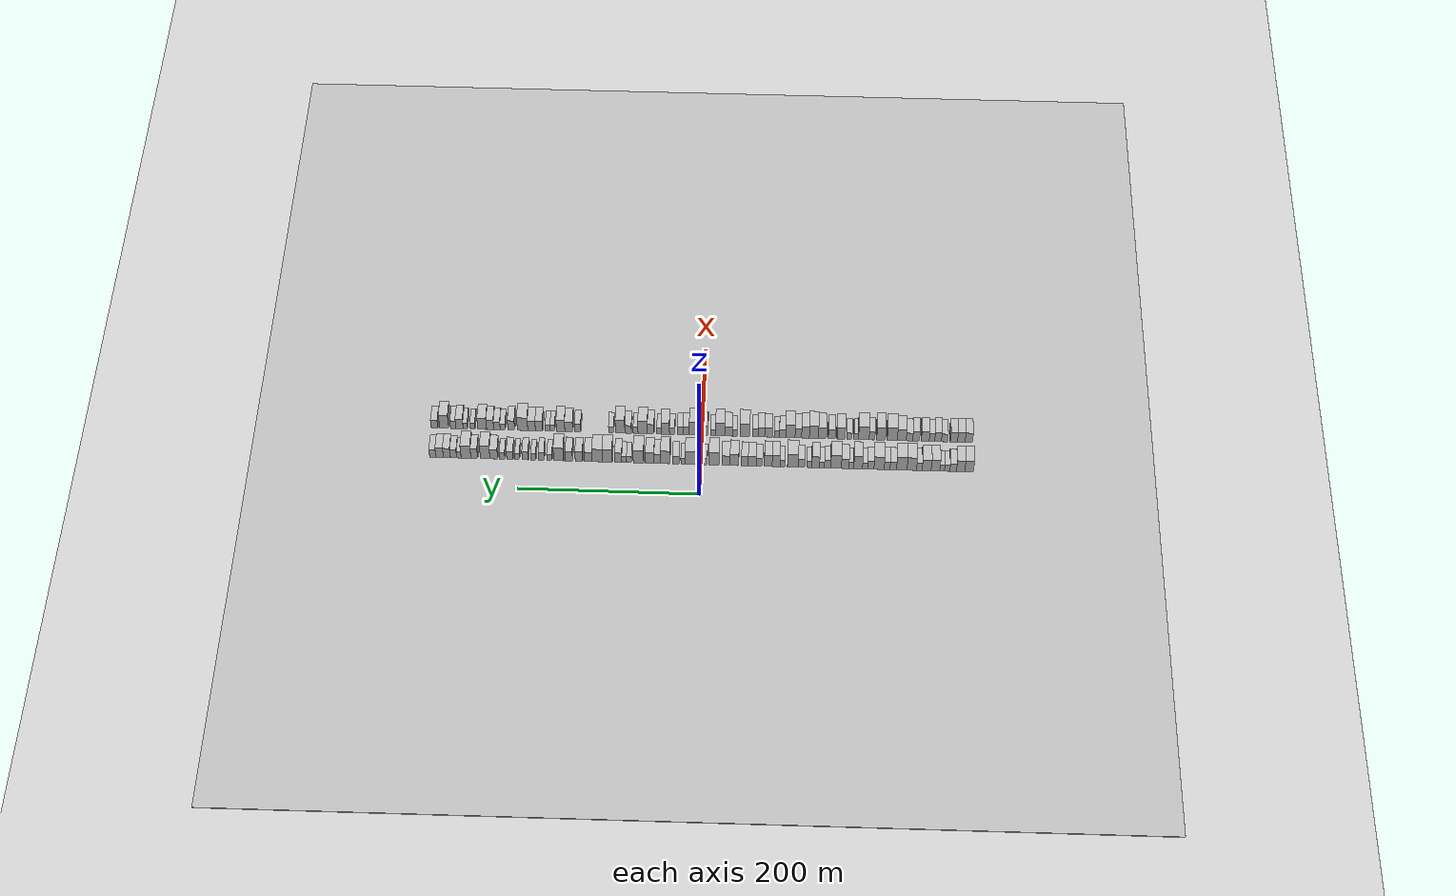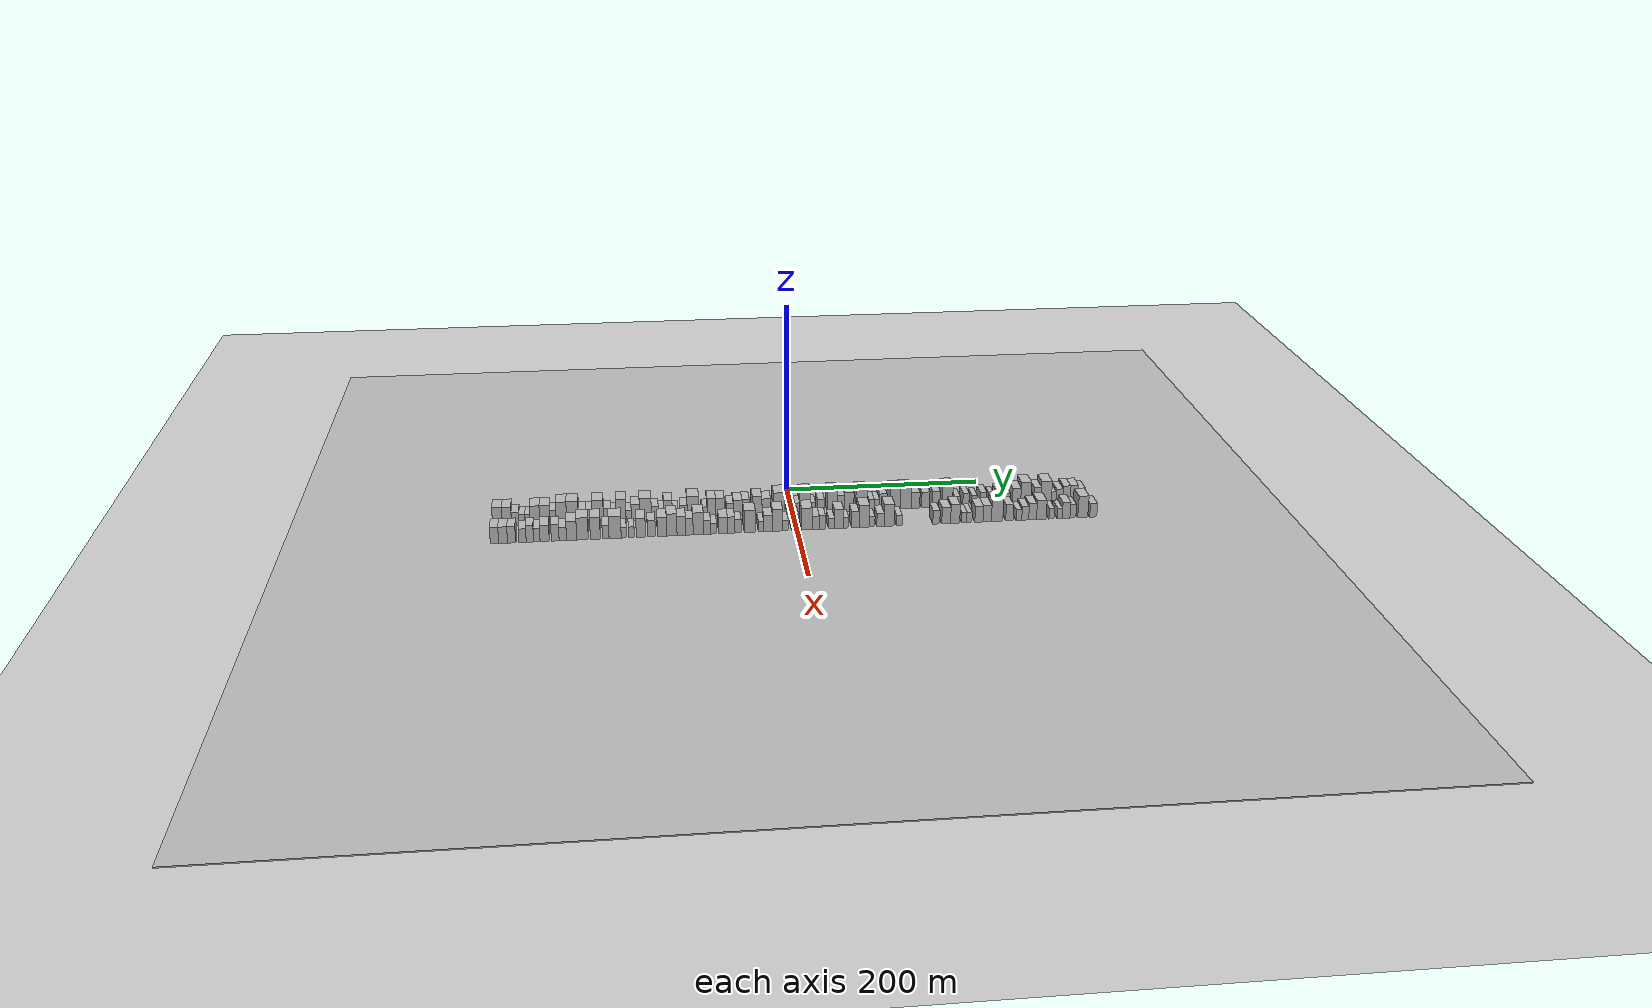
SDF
<?xml version="1.0" encoding="utf-8"?>

<sdf version="1.6">

   <world name="default">

      <gui fullscreen="0">

         <camera name="user_camera">

            <pose>-15 0 4.57585 0 0 0</pose>

            <view_controller>orbit</view_controller>

         </camera>

      </gui>

      <scene>

         <sky>

           <clouds>

             <speed>12</speed>

           </clouds>

         </sky>

         <ambient>0.4 0.4 0.4 1</ambient>

         <background>0.7 0.7 0.7 1</background>

         <shadows>1</shadows>

      </scene>

      <gravity>0 0 -9.8066</gravity>

      <magnetic_field>6e-06 2.3e-05 -4.2e-05</magnetic_field>

      <physics default="0" name="default_physics" type="ode">

         <ode>

            <solver>

               <type>quick</type>

               <iters>10</iters>

               <sor>1.0</sor>

               <use_dynamic_moi_rescaling>0</use_dynamic_moi_rescaling>

            </solver>

            <constraints>

               <cfm>0</cfm>

               <erp>0.2</erp>

               <contact_max_correcting_vel>100</contact_max_correcting_vel>

               <contact_surface_layer>0.001</contact_surface_layer>

            </constraints>

         </ode>

         <max_step_size>0.004</max_step_size>

         <real_time_factor>1</real_time_factor>

         <real_time_update_rate>250</real_time_update_rate>

      </physics>

      <light name="sun" type="directional">

         <cast_shadows>1</cast_shadows>

         <pose>0 0 10 0 0 0</pose>

         <diffuse>0.8 0.8 0.8 1</diffuse>

         <specular>0.2 0.2 0.2 1</specular>

         <attenuation>

            <range>1000</range>

            <constant>0.9</constant>

            <linear>0.01</linear>

            <quadratic>0.001</quadratic>

         </attenuation>

         <direction>-0.5 0.1 -0.9</direction>

      </light>

      <include>

         <name>ground_plane_1</name>

         <uri>model://HANNAS_ground_plane</uri>

         <pose>0 0 0  0 0 0</pose>

      </include>

      <include>

         <name>ground_plane_2</name>

         <uri>model://HANNAS_ground_plane</uri>

         <pose>100 0 0  0 0 0</pose>

      </include>

      <model name="building_1">

         <static>1</static>

         <pose frame="">50.0000 -295.1970 0 0.000000 0.000000 0.000000</pose>

         <link name="link">

            <pose frame="">0 0 10.50 0 0 0</pose>

            <collision name="collision">

               <geometry>

                  <box>

                     <size>20.0000 9.6060 21.0000</size>

                  </box>

               </geometry>

               <max_contacts>10</max_contacts>

               <surface>

                  <contact>

                     <ode/>

                  </contact>

                  <bounce/>

                  <friction>

                     <torsional>

                        <ode/>

                     </torsional>

                     <ode/>

                  </friction>

               </surface>

            </collision>

            <visual name="visual">

               <cast_shadows>0</cast_shadows>

               <geometry>

                  <box>

                     <size>20.0000 9.6060 21.0000</size>

                  </box>

               </geometry>

               <material>

                  <script>

                     <uri>model://HANNAS_wall/materials/scripts</uri>

                     <uri>model://HANNAS_wall/materials/textures</uri>

                     <name>vrc/HANNAS_wall</name>

                  </script>

               </material>

            </visual>

            <self_collide>0</self_collide>

            <enable_wind>0</enable_wind>

            <kinematic>0</kinematic>

         </link>

      </model>

      <model name="building_2">

         <static>1</static>

         <pose frame="">50.0000 -285.8825 0 0.000000 0.000000 0.000000</pose>

         <link name="link">

            <pose frame="">0 0 10.50 0 0 0</pose>

            <collision name="collision">

               <geometry>

                  <box>

                     <size>20.0000 9.0231 21.0000</size>

                  </box>

               </geometry>

               <max_contacts>10</max_contacts>

               <surface>

                  <contact>

                     <ode/>

                  </contact>

                  <bounce/>

                  <friction>

                     <torsional>

                        <ode/>

                     </torsional>

                     <ode/>

                  </friction>

               </surface>

            </collision>

            <visual name="visual">

               <cast_shadows>0</cast_shadows>

               <geometry>

                  <box>

                     <size>20.0000 9.0231 21.0000</size>

                  </box>

               </geometry>

               <material>

                  <script>

                     <uri>model://HANNAS_wall/materials/scripts</uri>

                     <uri>model://HANNAS_wall/materials/textures</uri>

                     <name>vrc/HANNAS_wall</name>

                  </script>

               </material>

            </visual>

            <self_collide>0</self_collide>

            <enable_wind>0</enable_wind>

            <kinematic>0</kinematic>

         </link>

      </model>

      <model name="building_3">

         <static>1</static>

         <pose frame="">50.0000 -277.6992 0 0.000000 0.000000 0.000000</pose>

         <link name="link">

            <pose frame="">0 0 7.50 0 0 0</pose>

            <collision name="collision">

               <geometry>

                  <box>

                     <size>20.0000 7.3435 15.0000</size>

                  </box>

               </geometry>

               <max_contacts>10</max_contacts>

               <surface>

                  <contact>

                     <ode/>

                  </contact>

                  <bounce/>

                  <friction>

                     <torsional>

                        <ode/>

                     </torsional>

                     <ode/>

                  </friction>

               </surface>

            </collision>

            <visual name="visual">

               <cast_shadows>0</cast_shadows>

               <geometry>

                  <box>

                     <size>20.0000 7.3435 15.0000</size>

                  </box>

               </geometry>

               <material>

                  <script>

                     <uri>model://HANNAS_wall/materials/scripts</uri>

                     <uri>model://HANNAS_wall/materials/textures</uri>

                     <name>vrc/HANNAS_wall</name>

                  </script>

               </material>

            </visual>

            <self_collide>0</self_collide>

            <enable_wind>0</enable_wind>

            <kinematic>0</kinematic>

         </link>

      </model>

      <model name="building_4">

         <static>1</static>

         <pose frame="">50.0000 -271.0660 0 0.000000 0.000000 0.000000</pose>

         <link name="link">

            <pose frame="">0 0 6.00 0 0 0</pose>

            <collision name="collision">

               <geometry>

                  <box>

                     <size>20.0000 5.9230 12.0000</size>

                  </box>

               </geometry>

               <max_contacts>10</max_contacts>

               <surface>

                  <contact>

                     <ode/>

                  </contact>

                  <bounce/>

                  <friction>

                     <torsional>

                        <ode/>

                     </torsional>

                     <ode/>

                  </friction>

               </surface>

            </collision>

            <visual name="visual">

               <cast_shadows>0</cast_shadows>

               <geometry>

                  <box>

                     <size>20.0000 5.9230 12.0000</size>

                  </box>

               </geometry>

               <material>

                  <script>

                     <uri>model://HANNAS_wall/materials/scripts</uri>

                     <uri>model://HANNAS_wall/materials/textures</uri>

                     <name>vrc/HANNAS_wall</name>

                  </script>

               </material>

            </visual>

            <self_collide>0</self_collide>

            <enable_wind>0</enable_wind>

            <kinematic>0</kinematic>

         </link>

      </model>

      <model name="building_5">

         <static>1</static>

         <pose frame="">50.0000 -265.5462 0 0.000000 0.000000 0.000000</pose>

         <link name="link">

            <pose frame="">0 0 6.00 0 0 0</pose>

            <collision name="collision">

               <geometry>

                  <box>

                     <size>20.0000 5.1166 12.0000</size>

                  </box>

               </geometry>

               <max_contacts>10</max_contacts>

               <surface>

                  <contact>

                     <ode/>

                  </contact>

                  <bounce/>

                  <friction>

                     <torsional>

                        <ode/>

                     </torsional>

                     <ode/>

                  </friction>

               </surface>

            </collision>

            <visual name="visual">

               <cast_shadows>0</cast_shadows>

               <geometry>

                  <box>

                     <size>20.0000 5.1166 12.0000</size>

                  </box>

               </geometry>

               <material>

                  <script>

                     <uri>model://HANNAS_wall/materials/scripts</uri>

                     <uri>model://HANNAS_wall/materials/textures</uri>

                     <name>vrc/HANNAS_wall</name>

                  </script>

               </material>

            </visual>

            <self_collide>0</self_collide>

            <enable_wind>0</enable_wind>

            <kinematic>0</kinematic>

         </link>

      </model>

      <model name="building_6">

         <static>1</static>

         <pose frame="">50.0000 -258.2183 0 0.000000 0.000000 0.000000</pose>

         <link name="link">

            <pose frame="">0 0 10.50 0 0 0</pose>

            <collision name="collision">

               <geometry>

                  <box>

                     <size>20.0000 9.5392 21.0000</size>

                  </box>

               </geometry>

               <max_contacts>10</max_contacts>

               <surface>

                  <contact>

                     <ode/>

                  </contact>

                  <bounce/>

                  <friction>

                     <torsional>

                        <ode/>

                     </torsional>

                     <ode/>

                  </friction>

               </surface>

            </collision>

            <visual name="visual">

               <cast_shadows>0</cast_shadows>

               <geometry>

                  <box>

                     <size>20.0000 9.5392 21.0000</size>

                  </box>

               </geometry>

               <material>

                  <script>

                     <uri>model://HANNAS_wall/materials/scripts</uri>

                     <uri>model://HANNAS_wall/materials/textures</uri>

                     <name>vrc/HANNAS_wall</name>

                  </script>

               </material>

            </visual>

            <self_collide>0</self_collide>

            <enable_wind>0</enable_wind>

            <kinematic>0</kinematic>

         </link>

      </model>

      <model name="building_7">

         <static>1</static>

         <pose frame="">50.0000 -248.4536 0 0.000000 0.000000 0.000000</pose>

         <link name="link">

            <pose frame="">0 0 10.50 0 0 0</pose>

            <collision name="collision">

               <geometry>

                  <box>

                     <size>20.0000 9.9902 21.0000</size>

                  </box>

               </geometry>

               <max_contacts>10</max_contacts>

               <surface>

                  <contact>

                     <ode/>

                  </contact>

                  <bounce/>

                  <friction>

                     <torsional>

                        <ode/>

                     </torsional>

                     <ode/>

                  </friction>

               </surface>

            </collision>

            <visual name="visual">

               <cast_shadows>0</cast_shadows>

               <geometry>

                  <box>

                     <size>20.0000 9.9902 21.0000</size>

                  </box>

               </geometry>

               <material>

                  <script>

                     <uri>model://HANNAS_wall/materials/scripts</uri>

                     <uri>model://HANNAS_wall/materials/textures</uri>

                     <name>vrc/HANNAS_wall</name>

                  </script>

               </material>

            </visual>

            <self_collide>0</self_collide>

            <enable_wind>0</enable_wind>

            <kinematic>0</kinematic>

         </link>

      </model>

      <model name="building_8">

         <static>1</static>

         <pose frame="">50.0000 -240.3835 0 0.000000 0.000000 0.000000</pose>

         <link name="link">

            <pose frame="">0 0 7.50 0 0 0</pose>

            <collision name="collision">

               <geometry>

                  <box>

                     <size>20.0000 6.1500 15.0000</size>

                  </box>

               </geometry>

               <max_contacts>10</max_contacts>

               <surface>

                  <contact>

                     <ode/>

                  </contact>

                  <bounce/>

                  <friction>

                     <torsional>

                        <ode/>

                     </torsional>

                     <ode/>

                  </friction>

               </surface>

            </collision>

            <visual name="visual">

               <cast_shadows>0</cast_shadows>

               <geometry>

                  <box>

                     <size>20.0000 6.1500 15.0000</size>

                  </box>

               </geometry>

               <material>

                  <script>

                     <uri>model://HANNAS_wall/materials/scripts</uri>

                     <uri>model://HANNAS_wall/materials/textures</uri>

                     <name>vrc/HANNAS_wall</name>

                  </script>

               </material>

            </visual>

            <self_collide>0</self_collide>

            <enable_wind>0</enable_wind>

            <kinematic>0</kinematic>

         </link>

      </model>

      <model name="building_9">

         <static>1</static>

         <pose frame="">50.0000 -232.0826 0 0.000000 0.000000 0.000000</pose>

         <link name="link">

            <pose frame="">0 0 12.00 0 0 0</pose>

            <collision name="collision">

               <geometry>

                  <box>

                     <size>20.0000 10.4518 24.0000</size>

                  </box>

               </geometry>

               <max_contacts>10</max_contacts>

               <surface>

                  <contact>

                     <ode/>

                  </contact>

                  <bounce/>

                  <friction>

                     <torsional>

                        <ode/>

                     </torsional>

                     <ode/>

                  </friction>

               </surface>

            </collision>

            <visual name="visual">

               <cast_shadows>0</cast_shadows>

               <geometry>

                  <box>

                     <size>20.0000 10.4518 24.0000</size>

                  </box>

               </geometry>

               <material>

                  <script>

                     <uri>model://HANNAS_wall/materials/scripts</uri>

                     <uri>model://HANNAS_wall/materials/textures</uri>

                     <name>vrc/HANNAS_wall</name>

                  </script>

               </material>

            </visual>

            <self_collide>0</self_collide>

            <enable_wind>0</enable_wind>

            <kinematic>0</kinematic>

         </link>

      </model>

      <model name="building_10">

         <static>1</static>

         <pose frame="">50.0000 -221.0790 0 0.000000 0.000000 0.000000</pose>

         <link name="link">

            <pose frame="">0 0 12.00 0 0 0</pose>

            <collision name="collision">

               <geometry>

                  <box>

                     <size>20.0000 11.5555 24.0000</size>

                  </box>

               </geometry>

               <max_contacts>10</max_contacts>

               <surface>

                  <contact>

                     <ode/>

                  </contact>

                  <bounce/>

                  <friction>

                     <torsional>

                        <ode/>

                     </torsional>

                     <ode/>

                  </friction>

               </surface>

            </collision>

            <visual name="visual">

               <cast_shadows>0</cast_shadows>

               <geometry>

                  <box>

                     <size>20.0000 11.5555 24.0000</size>

                  </box>

               </geometry>

               <material>

                  <script>

                     <uri>model://HANNAS_wall/materials/scripts</uri>

                     <uri>model://HANNAS_wall/materials/textures</uri>

                     <name>vrc/HANNAS_wall</name>

                  </script>

               </material>

            </visual>

            <self_collide>0</self_collide>

            <enable_wind>0</enable_wind>

            <kinematic>0</kinematic>

         </link>

      </model>

      <model name="building_11">

         <static>1</static>

         <pose frame="">50.0000 -211.6667 0 0.000000 0.000000 0.000000</pose>

         <link name="link">

            <pose frame="">0 0 7.50 0 0 0</pose>

            <collision name="collision">

               <geometry>

                  <box>

                     <size>20.0000 7.2691 15.0000</size>

                  </box>

               </geometry>

               <max_contacts>10</max_contacts>

               <surface>

                  <contact>

                     <ode/>

                  </contact>

                  <bounce/>

                  <friction>

                     <torsional>

                        <ode/>

                     </torsional>

                     <ode/>

                  </friction>

               </surface>

            </collision>

            <visual name="visual">

               <cast_shadows>0</cast_shadows>

               <geometry>

                  <box>

                     <size>20.0000 7.2691 15.0000</size>

                  </box>

               </geometry>

               <material>

                  <script>

                     <uri>model://HANNAS_wall/materials/scripts</uri>

                     <uri>model://HANNAS_wall/materials/textures</uri>

                     <name>vrc/HANNAS_wall</name>

                  </script>

               </material>

            </visual>

            <self_collide>0</self_collide>

            <enable_wind>0</enable_wind>

            <kinematic>0</kinematic>

         </link>

      </model>

      <model name="building_12">

         <static>1</static>

         <pose frame="">50.0000 -204.8449 0 0.000000 0.000000 0.000000</pose>

         <link name="link">

            <pose frame="">0 0 7.50 0 0 0</pose>

            <collision name="collision">

               <geometry>

                  <box>

                     <size>20.0000 6.3745 15.0000</size>

                  </box>

               </geometry>

               <max_contacts>10</max_contacts>

               <surface>

                  <contact>

                     <ode/>

                  </contact>

                  <bounce/>

                  <friction>

                     <torsional>

                        <ode/>

                     </torsional>

                     <ode/>

                  </friction>

               </surface>

            </collision>

            <visual name="visual">

               <cast_shadows>0</cast_shadows>

               <geometry>

                  <box>

                     <size>20.0000 6.3745 15.0000</size>

                  </box>

               </geometry>

               <material>

                  <script>

                     <uri>model://HANNAS_wall/materials/scripts</uri>

                     <uri>model://HANNAS_wall/materials/textures</uri>

                     <name>vrc/HANNAS_wall</name>

                  </script>

               </material>

            </visual>

            <self_collide>0</self_collide>

            <enable_wind>0</enable_wind>

            <kinematic>0</kinematic>

         </link>

      </model>

      <model name="building_13">

         <static>1</static>

         <pose frame="">50.0000 -196.0315 0 0.000000 0.000000 0.000000</pose>

         <link name="link">

            <pose frame="">0 0 12.00 0 0 0</pose>

            <collision name="collision">

               <geometry>

                  <box>

                     <size>20.0000 11.2523 24.0000</size>

                  </box>

               </geometry>

               <max_contacts>10</max_contacts>

               <surface>

                  <contact>

                     <ode/>

                  </contact>

                  <bounce/>

                  <friction>

                     <torsional>

                        <ode/>

                     </torsional>

                     <ode/>

                  </friction>

               </surface>

            </collision>

            <visual name="visual">

               <cast_shadows>0</cast_shadows>

               <geometry>

                  <box>

                     <size>20.0000 11.2523 24.0000</size>

                  </box>

               </geometry>

               <material>

                  <script>

                     <uri>model://HANNAS_wall/materials/scripts</uri>

                     <uri>model://HANNAS_wall/materials/textures</uri>

                     <name>vrc/HANNAS_wall</name>

                  </script>

               </material>

            </visual>

            <self_collide>0</self_collide>

            <enable_wind>0</enable_wind>

            <kinematic>0</kinematic>

         </link>

      </model>

      <model name="building_14">

         <static>1</static>

         <pose frame="">50.0000 -186.9027 0 0.000000 0.000000 0.000000</pose>

         <link name="link">

            <pose frame="">0 0 7.50 0 0 0</pose>

            <collision name="collision">

               <geometry>

                  <box>

                     <size>20.0000 7.0055 15.0000</size>

                  </box>

               </geometry>

               <max_contacts>10</max_contacts>

               <surface>

                  <contact>

                     <ode/>

                  </contact>

                  <bounce/>

                  <friction>

                     <torsional>

                        <ode/>

                     </torsional>

                     <ode/>

                  </friction>

               </surface>

            </collision>

            <visual name="visual">

               <cast_shadows>0</cast_shadows>

               <geometry>

                  <box>

                     <size>20.0000 7.0055 15.0000</size>

                  </box>

               </geometry>

               <material>

                  <script>

                     <uri>model://HANNAS_wall/materials/scripts</uri>

                     <uri>model://HANNAS_wall/materials/textures</uri>

                     <name>vrc/HANNAS_wall</name>

                  </script>

               </material>

            </visual>

            <self_collide>0</self_collide>

            <enable_wind>0</enable_wind>

            <kinematic>0</kinematic>

         </link>

      </model>

      <model name="building_15">

         <static>1</static>

         <pose frame="">50.0000 -180.5846 0 0.000000 0.000000 0.000000</pose>

         <link name="link">

            <pose frame="">0 0 6.00 0 0 0</pose>

            <collision name="collision">

               <geometry>

                  <box>

                     <size>20.0000 5.6305 12.0000</size>

                  </box>

               </geometry>

               <max_contacts>10</max_contacts>

               <surface>

                  <contact>

                     <ode/>

                  </contact>

                  <bounce/>

                  <friction>

                     <torsional>

                        <ode/>

                     </torsional>

                     <ode/>

                  </friction>

               </surface>

            </collision>

            <visual name="visual">

               <cast_shadows>0</cast_shadows>

               <geometry>

                  <box>

                     <size>20.0000 5.6305 12.0000</size>

                  </box>

               </geometry>

               <material>

                  <script>

                     <uri>model://HANNAS_wall/materials/scripts</uri>

                     <uri>model://HANNAS_wall/materials/textures</uri>

                     <name>vrc/HANNAS_wall</name>

                  </script>

               </material>

            </visual>

            <self_collide>0</self_collide>

            <enable_wind>0</enable_wind>

            <kinematic>0</kinematic>

         </link>

      </model>

      <model name="building_16">

         <static>1</static>

         <pose frame="">50.0000 -172.9262 0 0.000000 0.000000 0.000000</pose>

         <link name="link">

            <pose frame="">0 0 12.00 0 0 0</pose>

            <collision name="collision">

               <geometry>

                  <box>

                     <size>20.0000 9.6863 24.0000</size>

                  </box>

               </geometry>

               <max_contacts>10</max_contacts>

               <surface>

                  <contact>

                     <ode/>

                  </contact>

                  <bounce/>

                  <friction>

                     <torsional>

                        <ode/>

                     </torsional>

                     <ode/>

                  </friction>

               </surface>

            </collision>

            <visual name="visual">

               <cast_shadows>0</cast_shadows>

               <geometry>

                  <box>

                     <size>20.0000 9.6863 24.0000</size>

                  </box>

               </geometry>

               <material>

                  <script>

                     <uri>model://HANNAS_wall/materials/scripts</uri>

                     <uri>model://HANNAS_wall/materials/textures</uri>

                     <name>vrc/HANNAS_wall</name>

                  </script>

               </material>

            </visual>

            <self_collide>0</self_collide>

            <enable_wind>0</enable_wind>

            <kinematic>0</kinematic>

         </link>

      </model>

      <model name="building_17">

         <static>1</static>

         <pose frame="">50.0000 -165.3919 0 0.000000 0.000000 0.000000</pose>

         <link name="link">

            <pose frame="">0 0 6.00 0 0 0</pose>

            <collision name="collision">

               <geometry>

                  <box>

                     <size>20.0000 5.3823 12.0000</size>

                  </box>

               </geometry>

               <max_contacts>10</max_contacts>

               <surface>

                  <contact>

                     <ode/>

                  </contact>

                  <bounce/>

                  <friction>

                     <torsional>

                        <ode/>

                     </torsional>

                     <ode/>

                  </friction>

               </surface>

            </collision>

            <visual name="visual">

               <cast_shadows>0</cast_shadows>

               <geometry>

                  <box>

                     <size>20.0000 5.3823 12.0000</size>

                  </box>

               </geometry>

               <material>

                  <script>

                     <uri>model://HANNAS_wall/materials/scripts</uri>

                     <uri>model://HANNAS_wall/materials/textures</uri>

                     <name>vrc/HANNAS_wall</name>

                  </script>

               </material>

            </visual>

            <self_collide>0</self_collide>

            <enable_wind>0</enable_wind>

            <kinematic>0</kinematic>

         </link>

      </model>

      <model name="building_18">

         <static>1</static>

         <pose frame="">50.0000 -158.5544 0 0.000000 0.000000 0.000000</pose>

         <link name="link">

            <pose frame="">0 0 9.00 0 0 0</pose>

            <collision name="collision">

               <geometry>

                  <box>

                     <size>20.0000 8.2926 18.0000</size>

                  </box>

               </geometry>

               <max_contacts>10</max_contacts>

               <surface>

                  <contact>

                     <ode/>

                  </contact>

                  <bounce/>

                  <friction>

                     <torsional>

                        <ode/>

                     </torsional>

                     <ode/>

                  </friction>

               </surface>

            </collision>

            <visual name="visual">

               <cast_shadows>0</cast_shadows>

               <geometry>

                  <box>

                     <size>20.0000 8.2926 18.0000</size>

                  </box>

               </geometry>

               <material>

                  <script>

                     <uri>model://HANNAS_wall/materials/scripts</uri>

                     <uri>model://HANNAS_wall/materials/textures</uri>

                     <name>vrc/HANNAS_wall</name>

                  </script>

               </material>

            </visual>

            <self_collide>0</self_collide>

            <enable_wind>0</enable_wind>

            <kinematic>0</kinematic>

         </link>

      </model>

      <model name="building_19">

         <static>1</static>

         <pose frame="">50.0000 -148.5214 0 0.000000 0.000000 0.000000</pose>

         <link name="link">

            <pose frame="">0 0 12.00 0 0 0</pose>

            <collision name="collision">

               <geometry>

                  <box>

                     <size>20.0000 11.7735 24.0000</size>

                  </box>

               </geometry>

               <max_contacts>10</max_contacts>

               <surface>

                  <contact>

                     <ode/>

                  </contact>

                  <bounce/>

                  <friction>

                     <torsional>

                        <ode/>

                     </torsional>

                     <ode/>

                  </friction>

               </surface>

            </collision>

            <visual name="visual">

               <cast_shadows>0</cast_shadows>

               <geometry>

                  <box>

                     <size>20.0000 11.7735 24.0000</size>

                  </box>

               </geometry>

               <material>

                  <script>

                     <uri>model://HANNAS_wall/materials/scripts</uri>

                     <uri>model://HANNAS_wall/materials/textures</uri>

                     <name>vrc/HANNAS_wall</name>

                  </script>

               </material>

            </visual>

            <self_collide>0</self_collide>

            <enable_wind>0</enable_wind>

            <kinematic>0</kinematic>

         </link>

      </model>

      <model name="building_20">

         <static>1</static>

         <pose frame="">50.0000 -139.1447 0 0.000000 0.000000 0.000000</pose>

         <link name="link">

            <pose frame="">0 0 7.50 0 0 0</pose>

            <collision name="collision">

               <geometry>

                  <box>

                     <size>20.0000 6.9799 15.0000</size>

                  </box>

               </geometry>

               <max_contacts>10</max_contacts>

               <surface>

                  <contact>

                     <ode/>

                  </contact>

                  <bounce/>

                  <friction>

                     <torsional>

                        <ode/>

                     </torsional>

                     <ode/>

                  </friction>

               </surface>

            </collision>

            <visual name="visual">

               <cast_shadows>0</cast_shadows>

               <geometry>

                  <box>

                     <size>20.0000 6.9799 15.0000</size>

                  </box>

               </geometry>

               <material>

                  <script>

                     <uri>model://HANNAS_wall/materials/scripts</uri>

                     <uri>model://HANNAS_wall/materials/textures</uri>

                     <name>vrc/HANNAS_wall</name>

                  </script>

               </material>

            </visual>

            <self_collide>0</self_collide>

            <enable_wind>0</enable_wind>

            <kinematic>0</kinematic>

         </link>

      </model>

      <model name="building_21">

         <static>1</static>

         <pose frame="">50.0000 -132.9606 0 0.000000 0.000000 0.000000</pose>

         <link name="link">

            <pose frame="">0 0 6.00 0 0 0</pose>

            <collision name="collision">

               <geometry>

                  <box>

                     <size>20.0000 5.3883 12.0000</size>

                  </box>

               </geometry>

               <max_contacts>10</max_contacts>

               <surface>

                  <contact>

                     <ode/>

                  </contact>

                  <bounce/>

                  <friction>

                     <torsional>

                        <ode/>

                     </torsional>

                     <ode/>

                  </friction>

               </surface>

            </collision>

            <visual name="visual">

               <cast_shadows>0</cast_shadows>

               <geometry>

                  <box>

                     <size>20.0000 5.3883 12.0000</size>

                  </box>

               </geometry>

               <material>

                  <script>

                     <uri>model://HANNAS_wall/materials/scripts</uri>

                     <uri>model://HANNAS_wall/materials/textures</uri>

                     <name>vrc/HANNAS_wall</name>

                  </script>

               </material>

            </visual>

            <self_collide>0</self_collide>

            <enable_wind>0</enable_wind>

            <kinematic>0</kinematic>

         </link>

      </model>

      <model name="building_22">

         <static>1</static>

         <pose frame="">50.0000 -126.0294 0 0.000000 0.000000 0.000000</pose>

         <link name="link">

            <pose frame="">0 0 10.50 0 0 0</pose>

            <collision name="collision">

               <geometry>

                  <box>

                     <size>20.0000 8.4740 21.0000</size>

                  </box>

               </geometry>

               <max_contacts>10</max_contacts>

               <surface>

                  <contact>

                     <ode/>

                  </contact>

                  <bounce/>

                  <friction>

                     <torsional>

                        <ode/>

                     </torsional>

                     <ode/>

                  </friction>

               </surface>

            </collision>

            <visual name="visual">

               <cast_shadows>0</cast_shadows>

               <geometry>

                  <box>

                     <size>20.0000 8.4740 21.0000</size>

                  </box>

               </geometry>

               <material>

                  <script>

                     <uri>model://HANNAS_wall/materials/scripts</uri>

                     <uri>model://HANNAS_wall/materials/textures</uri>

                     <name>vrc/HANNAS_wall</name>

                  </script>

               </material>

            </visual>

            <self_collide>0</self_collide>

            <enable_wind>0</enable_wind>

            <kinematic>0</kinematic>

         </link>

      </model>

      <model name="building_23">

         <static>1</static>

         <pose frame="">50.0000 -118.9303 0 0.000000 0.000000 0.000000</pose>

         <link name="link">

            <pose frame="">0 0 6.00 0 0 0</pose>

            <collision name="collision">

               <geometry>

                  <box>

                     <size>20.0000 5.7242 12.0000</size>

                  </box>

               </geometry>

               <max_contacts>10</max_contacts>

               <surface>

                  <contact>

                     <ode/>

                  </contact>

                  <bounce/>

                  <friction>

                     <torsional>

                        <ode/>

                     </torsional>

                     <ode/>

                  </friction>

               </surface>

            </collision>

            <visual name="visual">

               <cast_shadows>0</cast_shadows>

               <geometry>

                  <box>

                     <size>20.0000 5.7242 12.0000</size>

                  </box>

               </geometry>

               <material>

                  <script>

                     <uri>model://HANNAS_wall/materials/scripts</uri>

                     <uri>model://HANNAS_wall/materials/textures</uri>

                     <name>vrc/HANNAS_wall</name>

                  </script>

               </material>

            </visual>

            <self_collide>0</self_collide>

            <enable_wind>0</enable_wind>

            <kinematic>0</kinematic>

         </link>

      </model>

      <model name="building_24">

         <static>1</static>

         <pose frame="">50.0000 -110.4495 0 0.000000 0.000000 0.000000</pose>

         <link name="link">

            <pose frame="">0 0 7.50 0 0 0</pose>

            <collision name="collision">

               <geometry>

                  <box>

                     <size>20.0000 7.2374 15.0000</size>

                  </box>

               </geometry>

               <max_contacts>10</max_contacts>

               <surface>

                  <contact>

                     <ode/>

                  </contact>

                  <bounce/>

                  <friction>

                     <torsional>

                        <ode/>

                     </torsional>

                     <ode/>

                  </friction>

               </surface>

            </collision>

            <visual name="visual">

               <cast_shadows>0</cast_shadows>

               <geometry>

                  <box>

                     <size>20.0000 7.2374 15.0000</size>

                  </box>

               </geometry>

               <material>

                  <script>

                     <uri>model://HANNAS_wall/materials/scripts</uri>

                     <uri>model://HANNAS_wall/materials/textures</uri>

                     <name>vrc/HANNAS_wall</name>

                  </script>

               </material>

            </visual>

            <self_collide>0</self_collide>

            <enable_wind>0</enable_wind>

            <kinematic>0</kinematic>

         </link>

      </model>

      <model name="building_25">

         <static>1</static>

         <pose frame="">50.0000 -100.9167 0 0.000000 0.000000 0.000000</pose>

         <link name="link">

            <pose frame="">0 0 12.00 0 0 0</pose>

            <collision name="collision">

               <geometry>

                  <box>

                     <size>20.0000 11.8284 24.0000</size>

                  </box>

               </geometry>

               <max_contacts>10</max_contacts>

               <surface>

                  <contact>

                     <ode/>

                  </contact>

                  <bounce/>

                  <friction>

                     <torsional>

                        <ode/>

                     </torsional>

                     <ode/>

                  </friction>

               </surface>

            </collision>

            <visual name="visual">

               <cast_shadows>0</cast_shadows>

               <geometry>

                  <box>

                     <size>20.0000 11.8284 24.0000</size>

                  </box>

               </geometry>

               <material>

                  <script>

                     <uri>model://HANNAS_wall/materials/scripts</uri>

                     <uri>model://HANNAS_wall/materials/textures</uri>

                     <name>vrc/HANNAS_wall</name>

                  </script>

               </material>

            </visual>

            <self_collide>0</self_collide>

            <enable_wind>0</enable_wind>

            <kinematic>0</kinematic>

         </link>

      </model>

      <model name="building_26">

         <static>1</static>

         <pose frame="">50.0000 -89.3581 0 0.000000 0.000000 0.000000</pose>

         <link name="link">

            <pose frame="">0 0 6.00 0 0 0</pose>

            <collision name="collision">

               <geometry>

                  <box>

                     <size>20.0000 5.2886 12.0000</size>

                  </box>

               </geometry>

               <max_contacts>10</max_contacts>

               <surface>

                  <contact>

                     <ode/>

                  </contact>

                  <bounce/>

                  <friction>

                     <torsional>

                        <ode/>

                     </torsional>

                     <ode/>

                  </friction>

               </surface>

            </collision>

            <visual name="visual">

               <cast_shadows>0</cast_shadows>

               <geometry>

                  <box>

                     <size>20.0000 5.2886 12.0000</size>

                  </box>

               </geometry>

               <material>

                  <script>

                     <uri>model://HANNAS_wall/materials/scripts</uri>

                     <uri>model://HANNAS_wall/materials/textures</uri>

                     <name>vrc/HANNAS_wall</name>

                  </script>

               </material>

            </visual>

            <self_collide>0</self_collide>

            <enable_wind>0</enable_wind>

            <kinematic>0</kinematic>

         </link>

      </model>

      <model name="building_27">

         <static>1</static>

         <pose frame="">50.0000 -82.3834 0 0.000000 0.000000 0.000000</pose>

         <link name="link">

            <pose frame="">0 0 10.50 0 0 0</pose>

            <collision name="collision">

               <geometry>

                  <box>

                     <size>20.0000 8.6609 21.0000</size>

                  </box>

               </geometry>

               <max_contacts>10</max_contacts>

               <surface>

                  <contact>

                     <ode/>

                  </contact>

                  <bounce/>

                  <friction>

                     <torsional>

                        <ode/>

                     </torsional>

                     <ode/>

                  </friction>

               </surface>

            </collision>

            <visual name="visual">

               <cast_shadows>0</cast_shadows>

               <geometry>

                  <box>

                     <size>20.0000 8.6609 21.0000</size>

                  </box>

               </geometry>

               <material>

                  <script>

                     <uri>model://HANNAS_wall/materials/scripts</uri>

                     <uri>model://HANNAS_wall/materials/textures</uri>

                     <name>vrc/HANNAS_wall</name>

                  </script>

               </material>

            </visual>

            <self_collide>0</self_collide>

            <enable_wind>0</enable_wind>

            <kinematic>0</kinematic>

         </link>

      </model>

      <model name="building_28">

         <static>1</static>

         <pose frame="">50.0000 -73.7411 0 0.000000 0.000000 0.000000</pose>

         <link name="link">

            <pose frame="">0 0 10.50 0 0 0</pose>

            <collision name="collision">

               <geometry>

                  <box>

                     <size>20.0000 8.6237 21.0000</size>

                  </box>

               </geometry>

               <max_contacts>10</max_contacts>

               <surface>

                  <contact>

                     <ode/>

                  </contact>

                  <bounce/>

                  <friction>

                     <torsional>

                        <ode/>

                     </torsional>

                     <ode/>

                  </friction>

               </surface>

            </collision>

            <visual name="visual">

               <cast_shadows>0</cast_shadows>

               <geometry>

                  <box>

                     <size>20.0000 8.6237 21.0000</size>

                  </box>

               </geometry>

               <material>

                  <script>

                     <uri>model://HANNAS_wall/materials/scripts</uri>

                     <uri>model://HANNAS_wall/materials/textures</uri>

                     <name>vrc/HANNAS_wall</name>

                  </script>

               </material>

            </visual>

            <self_collide>0</self_collide>

            <enable_wind>0</enable_wind>

            <kinematic>0</kinematic>

         </link>

      </model>

      <model name="building_29">

         <static>1</static>

         <pose frame="">50.0000 -63.8989 0 0.000000 0.000000 0.000000</pose>

         <link name="link">

            <pose frame="">0 0 7.50 0 0 0</pose>

            <collision name="collision">

               <geometry>

                  <box>

                     <size>20.0000 7.0606 15.0000</size>

                  </box>

               </geometry>

               <max_contacts>10</max_contacts>

               <surface>

                  <contact>

                     <ode/>

                  </contact>

                  <bounce/>

                  <friction>

                     <torsional>

                        <ode/>

                     </torsional>

                     <ode/>

                  </friction>

               </surface>

            </collision>

            <visual name="visual">

               <cast_shadows>0</cast_shadows>

               <geometry>

                  <box>

                     <size>20.0000 7.0606 15.0000</size>

                  </box>

               </geometry>

               <material>

                  <script>

                     <uri>model://HANNAS_wall/materials/scripts</uri>

                     <uri>model://HANNAS_wall/materials/textures</uri>

                     <name>vrc/HANNAS_wall</name>

                  </script>

               </material>

            </visual>

            <self_collide>0</self_collide>

            <enable_wind>0</enable_wind>

            <kinematic>0</kinematic>

         </link>

      </model>

      <model name="building_30">

         <static>1</static>

         <pose frame="">50.0000 -55.9622 0 0.000000 0.000000 0.000000</pose>

         <link name="link">

            <pose frame="">0 0 9.00 0 0 0</pose>

            <collision name="collision">

               <geometry>

                  <box>

                     <size>20.0000 8.8129 18.0000</size>

                  </box>

               </geometry>

               <max_contacts>10</max_contacts>

               <surface>

                  <contact>

                     <ode/>

                  </contact>

                  <bounce/>

                  <friction>

                     <torsional>

                        <ode/>

                     </torsional>

                     <ode/>

                  </friction>

               </surface>

            </collision>

            <visual name="visual">

               <cast_shadows>0</cast_shadows>

               <geometry>

                  <box>

                     <size>20.0000 8.8129 18.0000</size>

                  </box>

               </geometry>

               <material>

                  <script>

                     <uri>model://HANNAS_wall/materials/scripts</uri>

                     <uri>model://HANNAS_wall/materials/textures</uri>

                     <name>vrc/HANNAS_wall</name>

                  </script>

               </material>

            </visual>

            <self_collide>0</self_collide>

            <enable_wind>0</enable_wind>

            <kinematic>0</kinematic>

         </link>

      </model>

      <model name="building_31">

         <static>1</static>

         <pose frame="">50.0000 -47.8337 0 0.000000 0.000000 0.000000</pose>

         <link name="link">

            <pose frame="">0 0 9.00 0 0 0</pose>

            <collision name="collision">

               <geometry>

                  <box>

                     <size>20.0000 7.4441 18.0000</size>

                  </box>

               </geometry>

               <max_contacts>10</max_contacts>

               <surface>

                  <contact>

                     <ode/>

                  </contact>

                  <bounce/>

                  <friction>

                     <torsional>

                        <ode/>

                     </torsional>

                     <ode/>

                  </friction>

               </surface>

            </collision>

            <visual name="visual">

               <cast_shadows>0</cast_shadows>

               <geometry>

                  <box>

                     <size>20.0000 7.4441 18.0000</size>

                  </box>

               </geometry>

               <material>

                  <script>

                     <uri>model://HANNAS_wall/materials/scripts</uri>

                     <uri>model://HANNAS_wall/materials/textures</uri>

                     <name>vrc/HANNAS_wall</name>

                  </script>

               </material>

            </visual>

            <self_collide>0</self_collide>

            <enable_wind>0</enable_wind>

            <kinematic>0</kinematic>

         </link>

      </model>

      <model name="building_32">

         <static>1</static>

         <pose frame="">50.0000 -36.3141 0 0.000000 0.000000 0.000000</pose>

         <link name="link">

            <pose frame="">0 0 10.50 0 0 0</pose>

            <collision name="collision">

               <geometry>

                  <box>

                     <size>20.0000 9.5950 21.0000</size>

                  </box>

               </geometry>

               <max_contacts>10</max_contacts>

               <surface>

                  <contact>

                     <ode/>

                  </contact>

                  <bounce/>

                  <friction>

                     <torsional>

                        <ode/>

                     </torsional>

                     <ode/>

                  </friction>

               </surface>

            </collision>

            <visual name="visual">

               <cast_shadows>0</cast_shadows>

               <geometry>

                  <box>

                     <size>20.0000 9.5950 21.0000</size>

                  </box>

               </geometry>

               <material>

                  <script>

                     <uri>model://HANNAS_wall/materials/scripts</uri>

                     <uri>model://HANNAS_wall/materials/textures</uri>

                     <name>vrc/HANNAS_wall</name>

                  </script>

               </material>

            </visual>

            <self_collide>0</self_collide>

            <enable_wind>0</enable_wind>

            <kinematic>0</kinematic>

         </link>

      </model>

      <model name="building_33">

         <static>1</static>

         <pose frame="">50.0000 -27.0605 0 0.000000 0.000000 0.000000</pose>

         <link name="link">

            <pose frame="">0 0 9.00 0 0 0</pose>

            <collision name="collision">

               <geometry>

                  <box>

                     <size>20.0000 8.9123 18.0000</size>

                  </box>

               </geometry>

               <max_contacts>10</max_contacts>

               <surface>

                  <contact>

                     <ode/>

                  </contact>

                  <bounce/>

                  <friction>

                     <torsional>

                        <ode/>

                     </torsional>

                     <ode/>

                  </friction>

               </surface>

            </collision>

            <visual name="visual">

               <cast_shadows>0</cast_shadows>

               <geometry>

                  <box>

                     <size>20.0000 8.9123 18.0000</size>

                  </box>

               </geometry>

               <material>

                  <script>

                     <uri>model://HANNAS_wall/materials/scripts</uri>

                     <uri>model://HANNAS_wall/materials/textures</uri>

                     <name>vrc/HANNAS_wall</name>

                  </script>

               </material>

            </visual>

            <self_collide>0</self_collide>

            <enable_wind>0</enable_wind>

            <kinematic>0</kinematic>

         </link>

      </model>

      <model name="building_34">

         <static>1</static>

         <pose frame="">50.0000 -13.9487 0 0.000000 0.000000 0.000000</pose>

         <link name="link">

            <pose frame="">0 0 12.00 0 0 0</pose>

            <collision name="collision">

               <geometry>

                  <box>

                     <size>20.0000 11.3113 24.0000</size>

                  </box>

               </geometry>

               <max_contacts>10</max_contacts>

               <surface>

                  <contact>

                     <ode/>

                  </contact>

                  <bounce/>

                  <friction>

                     <torsional>

                        <ode/>

                     </torsional>

                     <ode/>

                  </friction>

               </surface>

            </collision>

            <visual name="visual">

               <cast_shadows>0</cast_shadows>

               <geometry>

                  <box>

                     <size>20.0000 11.3113 24.0000</size>

                  </box>

               </geometry>

               <material>

                  <script>

                     <uri>model://HANNAS_wall/materials/scripts</uri>

                     <uri>model://HANNAS_wall/materials/textures</uri>

                     <name>vrc/HANNAS_wall</name>

                  </script>

               </material>

            </visual>

            <self_collide>0</self_collide>

            <enable_wind>0</enable_wind>

            <kinematic>0</kinematic>

         </link>

      </model>

      <model name="building_35">

         <static>1</static>

         <pose frame="">50.0000 -3.7508 0 0.000000 0.000000 0.000000</pose>

         <link name="link">

            <pose frame="">0 0 6.00 0 0 0</pose>

            <collision name="collision">

               <geometry>

                  <box>

                     <size>20.0000 5.0844 12.0000</size>

                  </box>

               </geometry>

               <max_contacts>10</max_contacts>

               <surface>

                  <contact>

                     <ode/>

                  </contact>

                  <bounce/>

                  <friction>

                     <torsional>

                        <ode/>

                     </torsional>

                     <ode/>

                  </friction>

               </surface>

            </collision>

            <visual name="visual">

               <cast_shadows>0</cast_shadows>

               <geometry>

                  <box>

                     <size>20.0000 5.0844 12.0000</size>

                  </box>

               </geometry>

               <material>

                  <script>

                     <uri>model://HANNAS_wall/materials/scripts</uri>

                     <uri>model://HANNAS_wall/materials/textures</uri>

                     <name>vrc/HANNAS_wall</name>

                  </script>

               </material>

            </visual>

            <self_collide>0</self_collide>

            <enable_wind>0</enable_wind>

            <kinematic>0</kinematic>

         </link>

      </model>

      <model name="building_36">

         <static>1</static>

         <pose frame="">50.0000 4.3104 0 0.000000 0.000000 0.000000</pose>

         <link name="link">

            <pose frame="">0 0 6.00 0 0 0</pose>

            <collision name="collision">

               <geometry>

                  <box>

                     <size>20.0000 5.0379 12.0000</size>

                  </box>

               </geometry>

               <max_contacts>10</max_contacts>

               <surface>

                  <contact>

                     <ode/>

                  </contact>

                  <bounce/>

                  <friction>

                     <torsional>

                        <ode/>

                     </torsional>

                     <ode/>

                  </friction>

               </surface>

            </collision>

            <visual name="visual">

               <cast_shadows>0</cast_shadows>

               <geometry>

                  <box>

                     <size>20.0000 5.0379 12.0000</size>

                  </box>

               </geometry>

               <material>

                  <script>

                     <uri>model://HANNAS_wall/materials/scripts</uri>

                     <uri>model://HANNAS_wall/materials/textures</uri>

                     <name>vrc/HANNAS_wall</name>

                  </script>

               </material>

            </visual>

            <self_collide>0</self_collide>

            <enable_wind>0</enable_wind>

            <kinematic>0</kinematic>

         </link>

      </model>

      <model name="building_37">

         <static>1</static>

         <pose frame="">50.0000 12.4003 0 0.000000 0.000000 0.000000</pose>

         <link name="link">

            <pose frame="">0 0 12.00 0 0 0</pose>

            <collision name="collision">

               <geometry>

                  <box>

                     <size>20.0000 11.1420 24.0000</size>

                  </box>

               </geometry>

               <max_contacts>10</max_contacts>

               <surface>

                  <contact>

                     <ode/>

                  </contact>

                  <bounce/>

                  <friction>

                     <torsional>

                        <ode/>

                     </torsional>

                     <ode/>

                  </friction>

               </surface>

            </collision>

            <visual name="visual">

               <cast_shadows>0</cast_shadows>

               <geometry>

                  <box>

                     <size>20.0000 11.1420 24.0000</size>

                  </box>

               </geometry>

               <material>

                  <script>

                     <uri>model://HANNAS_wall/materials/scripts</uri>

                     <uri>model://HANNAS_wall/materials/textures</uri>

                     <name>vrc/HANNAS_wall</name>

                  </script>

               </material>

            </visual>

            <self_collide>0</self_collide>

            <enable_wind>0</enable_wind>

            <kinematic>0</kinematic>

         </link>

      </model>

      <model name="building_38">

         <static>1</static>

         <pose frame="">50.0000 20.3887 0 0.000000 0.000000 0.000000</pose>

         <link name="link">

            <pose frame="">0 0 6.00 0 0 0</pose>

            <collision name="collision">

               <geometry>

                  <box>

                     <size>20.0000 4.8348 12.0000</size>

                  </box>

               </geometry>

               <max_contacts>10</max_contacts>

               <surface>

                  <contact>

                     <ode/>

                  </contact>

                  <bounce/>

                  <friction>

                     <torsional>

                        <ode/>

                     </torsional>

                     <ode/>

                  </friction>

               </surface>

            </collision>

            <visual name="visual">

               <cast_shadows>0</cast_shadows>

               <geometry>

                  <box>

                     <size>20.0000 4.8348 12.0000</size>

                  </box>

               </geometry>

               <material>

                  <script>

                     <uri>model://HANNAS_wall/materials/scripts</uri>

                     <uri>model://HANNAS_wall/materials/textures</uri>

                     <name>vrc/HANNAS_wall</name>

                  </script>

               </material>

            </visual>

            <self_collide>0</self_collide>

            <enable_wind>0</enable_wind>

            <kinematic>0</kinematic>

         </link>

      </model>

      <model name="building_39">

         <static>1</static>

         <pose frame="">50.0000 28.3555 0 0.000000 0.000000 0.000000</pose>

         <link name="link">

            <pose frame="">0 0 7.50 0 0 0</pose>

            <collision name="collision">

               <geometry>

                  <box>

                     <size>20.0000 7.0989 15.0000</size>

                  </box>

               </geometry>

               <max_contacts>10</max_contacts>

               <surface>

                  <contact>

                     <ode/>

                  </contact>

                  <bounce/>

                  <friction>

                     <torsional>

                        <ode/>

                     </torsional>

                     <ode/>

                  </friction>

               </surface>

            </collision>

            <visual name="visual">

               <cast_shadows>0</cast_shadows>

               <geometry>

                  <box>

                     <size>20.0000 7.0989 15.0000</size>

                  </box>

               </geometry>

               <material>

                  <script>

                     <uri>model://HANNAS_wall/materials/scripts</uri>

                     <uri>model://HANNAS_wall/materials/textures</uri>

                     <name>vrc/HANNAS_wall</name>

                  </script>

               </material>

            </visual>

            <self_collide>0</self_collide>

            <enable_wind>0</enable_wind>

            <kinematic>0</kinematic>

         </link>

      </model>

      <model name="building_40">

         <static>1</static>

         <pose frame="">50.0000 40.0406 0 0.000000 0.000000 0.000000</pose>

         <link name="link">

            <pose frame="">0 0 12.00 0 0 0</pose>

            <collision name="collision">

               <geometry>

                  <box>

                     <size>20.0000 10.2713 24.0000</size>

                  </box>

               </geometry>

               <max_contacts>10</max_contacts>

               <surface>

                  <contact>

                     <ode/>

                  </contact>

                  <bounce/>

                  <friction>

                     <torsional>

                        <ode/>

                     </torsional>

                     <ode/>

                  </friction>

               </surface>

            </collision>

            <visual name="visual">

               <cast_shadows>0</cast_shadows>

               <geometry>

                  <box>

                     <size>20.0000 10.2713 24.0000</size>

                  </box>

               </geometry>

               <material>

                  <script>

                     <uri>model://HANNAS_wall/materials/scripts</uri>

                     <uri>model://HANNAS_wall/materials/textures</uri>

                     <name>vrc/HANNAS_wall</name>

                  </script>

               </material>

            </visual>

            <self_collide>0</self_collide>

            <enable_wind>0</enable_wind>

            <kinematic>0</kinematic>

         </link>

      </model>

      <model name="building_41">

         <static>1</static>

         <pose frame="">50.0000 48.8296 0 0.000000 0.000000 0.000000</pose>

         <link name="link">

            <pose frame="">0 0 9.00 0 0 0</pose>

            <collision name="collision">

               <geometry>

                  <box>

                     <size>20.0000 7.3065 18.0000</size>

                  </box>

               </geometry>

               <max_contacts>10</max_contacts>

               <surface>

                  <contact>

                     <ode/>

                  </contact>

                  <bounce/>

                  <friction>

                     <torsional>

                        <ode/>

                     </torsional>

                     <ode/>

                  </friction>

               </surface>

            </collision>

            <visual name="visual">

               <cast_shadows>0</cast_shadows>

               <geometry>

                  <box>

                     <size>20.0000 7.3065 18.0000</size>

                  </box>

               </geometry>

               <material>

                  <script>

                     <uri>model://HANNAS_wall/materials/scripts</uri>

                     <uri>model://HANNAS_wall/materials/textures</uri>

                     <name>vrc/HANNAS_wall</name>

                  </script>

               </material>

            </visual>

            <self_collide>0</self_collide>

            <enable_wind>0</enable_wind>

            <kinematic>0</kinematic>

         </link>

      </model>

      <model name="building_42">

         <static>1</static>

         <pose frame="">50.0000 57.1725 0 0.000000 0.000000 0.000000</pose>

         <link name="link">

            <pose frame="">0 0 10.50 0 0 0</pose>

            <collision name="collision">

               <geometry>

                  <box>

                     <size>20.0000 9.3794 21.0000</size>

                  </box>

               </geometry>

               <max_contacts>10</max_contacts>

               <surface>

                  <contact>

                     <ode/>

                  </contact>

                  <bounce/>

                  <friction>

                     <torsional>

                        <ode/>

                     </torsional>

                     <ode/>

                  </friction>

               </surface>

            </collision>

            <visual name="visual">

               <cast_shadows>0</cast_shadows>

               <geometry>

                  <box>

                     <size>20.0000 9.3794 21.0000</size>

                  </box>

               </geometry>

               <material>

                  <script>

                     <uri>model://HANNAS_wall/materials/scripts</uri>

                     <uri>model://HANNAS_wall/materials/textures</uri>

                     <name>vrc/HANNAS_wall</name>

                  </script>

               </material>

            </visual>

            <self_collide>0</self_collide>

            <enable_wind>0</enable_wind>

            <kinematic>0</kinematic>

         </link>

      </model>

      <model name="building_43">

         <static>1</static>

         <pose frame="">50.0000 69.6522 0 0.000000 0.000000 0.000000</pose>

         <link name="link">

            <pose frame="">0 0 12.00 0 0 0</pose>

            <collision name="collision">

               <geometry>

                  <box>

                     <size>20.0000 11.5799 24.0000</size>

                  </box>

               </geometry>

               <max_contacts>10</max_contacts>

               <surface>

                  <contact>

                     <ode/>

                  </contact>

                  <bounce/>

                  <friction>

                     <torsional>

                        <ode/>

                     </torsional>

                     <ode/>

                  </friction>

               </surface>

            </collision>

            <visual name="visual">

               <cast_shadows>0</cast_shadows>

               <geometry>

                  <box>

                     <size>20.0000 11.5799 24.0000</size>

                  </box>

               </geometry>

               <material>

                  <script>

                     <uri>model://HANNAS_wall/materials/scripts</uri>

                     <uri>model://HANNAS_wall/materials/textures</uri>

                     <name>vrc/HANNAS_wall</name>

                  </script>

               </material>

            </visual>

            <self_collide>0</self_collide>

            <enable_wind>0</enable_wind>

            <kinematic>0</kinematic>

         </link>

      </model>

      <model name="building_44">

         <static>1</static>

         <pose frame="">50.0000 80.1559 0 0.000000 0.000000 0.000000</pose>

         <link name="link">

            <pose frame="">0 0 6.00 0 0 0</pose>

            <collision name="collision">

               <geometry>

                  <box>

                     <size>20.0000 5.4277 12.0000</size>

                  </box>

               </geometry>

               <max_contacts>10</max_contacts>

               <surface>

                  <contact>

                     <ode/>

                  </contact>

                  <bounce/>

                  <friction>

                     <torsional>

                        <ode/>

                     </torsional>

                     <ode/>

                  </friction>

               </surface>

            </collision>

            <visual name="visual">

               <cast_shadows>0</cast_shadows>

               <geometry>

                  <box>

                     <size>20.0000 5.4277 12.0000</size>

                  </box>

               </geometry>

               <material>

                  <script>

                     <uri>model://HANNAS_wall/materials/scripts</uri>

                     <uri>model://HANNAS_wall/materials/textures</uri>

                     <name>vrc/HANNAS_wall</name>

                  </script>

               </material>

            </visual>

            <self_collide>0</self_collide>

            <enable_wind>0</enable_wind>

            <kinematic>0</kinematic>

         </link>

      </model>

      <model name="building_45">

         <static>1</static>

         <pose frame="">50.0000 85.5039 0 0.000000 0.000000 0.000000</pose>

         <link name="link">

            <pose frame="">0 0 6.00 0 0 0</pose>

            <collision name="collision">

               <geometry>

                  <box>

                     <size>20.0000 5.2683 12.0000</size>

                  </box>

               </geometry>

               <max_contacts>10</max_contacts>

               <surface>

                  <contact>

                     <ode/>

                  </contact>

                  <bounce/>

                  <friction>

                     <torsional>

                        <ode/>

                     </torsional>

                     <ode/>

                  </friction>

               </surface>

            </collision>

            <visual name="visual">

               <cast_shadows>0</cast_shadows>

               <geometry>

                  <box>

                     <size>20.0000 5.2683 12.0000</size>

                  </box>

               </geometry>

               <material>

                  <script>

                     <uri>model://HANNAS_wall/materials/scripts</uri>

                     <uri>model://HANNAS_wall/materials/textures</uri>

                     <name>vrc/HANNAS_wall</name>

                  </script>

               </material>

            </visual>

            <self_collide>0</self_collide>

            <enable_wind>0</enable_wind>

            <kinematic>0</kinematic>

         </link>

      </model>

      <model name="building_46">

         <static>1</static>

         <pose frame="">50.0000 91.9332 0 0.000000 0.000000 0.000000</pose>

         <link name="link">

            <pose frame="">0 0 9.00 0 0 0</pose>

            <collision name="collision">

               <geometry>

                  <box>

                     <size>20.0000 7.5904 18.0000</size>

                  </box>

               </geometry>

               <max_contacts>10</max_contacts>

               <surface>

                  <contact>

                     <ode/>

                  </contact>

                  <bounce/>

                  <friction>

                     <torsional>

                        <ode/>

                     </torsional>

                     <ode/>

                  </friction>

               </surface>

            </collision>

            <visual name="visual">

               <cast_shadows>0</cast_shadows>

               <geometry>

                  <box>

                     <size>20.0000 7.5904 18.0000</size>

                  </box>

               </geometry>

               <material>

                  <script>

                     <uri>model://HANNAS_wall/materials/scripts</uri>

                     <uri>model://HANNAS_wall/materials/textures</uri>

                     <name>vrc/HANNAS_wall</name>

                  </script>

               </material>

            </visual>

            <self_collide>0</self_collide>

            <enable_wind>0</enable_wind>

            <kinematic>0</kinematic>

         </link>

      </model>

      <model name="building_47">

         <static>1</static>

         <pose frame="">50.0000 104.1379 0 0.000000 0.000000 0.000000</pose>

         <link name="link">

            <pose frame="">0 0 12.00 0 0 0</pose>

            <collision name="collision">

               <geometry>

                  <box>

                     <size>20.0000 10.8189 24.0000</size>

                  </box>

               </geometry>

               <max_contacts>10</max_contacts>

               <surface>

                  <contact>

                     <ode/>

                  </contact>

                  <bounce/>

                  <friction>

                     <torsional>

                        <ode/>

                     </torsional>

                     <ode/>

                  </friction>

               </surface>

            </collision>

            <visual name="visual">

               <cast_shadows>0</cast_shadows>

               <geometry>

                  <box>

                     <size>20.0000 10.8189 24.0000</size>

                  </box>

               </geometry>

               <material>

                  <script>

                     <uri>model://HANNAS_wall/materials/scripts</uri>

                     <uri>model://HANNAS_wall/materials/textures</uri>

                     <name>vrc/HANNAS_wall</name>

                  </script>

               </material>

            </visual>

            <self_collide>0</self_collide>

            <enable_wind>0</enable_wind>

            <kinematic>0</kinematic>

         </link>

      </model>

      <model name="building_48">

         <static>1</static>

         <pose frame="">50.0000 115.2195 0 0.000000 0.000000 0.000000</pose>

         <link name="link">

            <pose frame="">0 0 12.00 0 0 0</pose>

            <collision name="collision">

               <geometry>

                  <box>

                     <size>20.0000 11.3442 24.0000</size>

                  </box>

               </geometry>

               <max_contacts>10</max_contacts>

               <surface>

                  <contact>

                     <ode/>

                  </contact>

                  <bounce/>

                  <friction>

                     <torsional>

                        <ode/>

                     </torsional>

                     <ode/>

                  </friction>

               </surface>

            </collision>

            <visual name="visual">

               <cast_shadows>0</cast_shadows>

               <geometry>

                  <box>

                     <size>20.0000 11.3442 24.0000</size>

                  </box>

               </geometry>

               <material>

                  <script>

                     <uri>model://HANNAS_wall/materials/scripts</uri>

                     <uri>model://HANNAS_wall/materials/textures</uri>

                     <name>vrc/HANNAS_wall</name>

                  </script>

               </material>

            </visual>

            <self_collide>0</self_collide>

            <enable_wind>0</enable_wind>

            <kinematic>0</kinematic>

         </link>

      </model>

      <model name="building_49">

         <static>1</static>

         <pose frame="">50.0000 125.1964 0 0.000000 0.000000 0.000000</pose>

         <link name="link">

            <pose frame="">0 0 9.00 0 0 0</pose>

            <collision name="collision">

               <geometry>

                  <box>

                     <size>20.0000 8.6096 18.0000</size>

                  </box>

               </geometry>

               <max_contacts>10</max_contacts>

               <surface>

                  <contact>

                     <ode/>

                  </contact>

                  <bounce/>

                  <friction>

                     <torsional>

                        <ode/>

                     </torsional>

                     <ode/>

                  </friction>

               </surface>

            </collision>

            <visual name="visual">

               <cast_shadows>0</cast_shadows>

               <geometry>

                  <box>

                     <size>20.0000 8.6096 18.0000</size>

                  </box>

               </geometry>

               <material>

                  <script>

                     <uri>model://HANNAS_wall/materials/scripts</uri>

                     <uri>model://HANNAS_wall/materials/textures</uri>

                     <name>vrc/HANNAS_wall</name>

                  </script>

               </material>

            </visual>

            <self_collide>0</self_collide>

            <enable_wind>0</enable_wind>

            <kinematic>0</kinematic>

         </link>

      </model>

      <model name="building_50">

         <static>1</static>

         <pose frame="">50.0000 135.5839 0 0.000000 0.000000 0.000000</pose>

         <link name="link">

            <pose frame="">0 0 9.00 0 0 0</pose>

            <collision name="collision">

               <geometry>

                  <box>

                     <size>20.0000 8.1655 18.0000</size>

                  </box>

               </geometry>

               <max_contacts>10</max_contacts>

               <surface>

                  <contact>

                     <ode/>

                  </contact>

                  <bounce/>

                  <friction>

                     <torsional>

                        <ode/>

                     </torsional>

                     <ode/>

                  </friction>

               </surface>

            </collision>

            <visual name="visual">

               <cast_shadows>0</cast_shadows>

               <geometry>

                  <box>

                     <size>20.0000 8.1655 18.0000</size>

                  </box>

               </geometry>

               <material>

                  <script>

                     <uri>model://HANNAS_wall/materials/scripts</uri>

                     <uri>model://HANNAS_wall/materials/textures</uri>

                     <name>vrc/HANNAS_wall</name>

                  </script>

               </material>

            </visual>

            <self_collide>0</self_collide>

            <enable_wind>0</enable_wind>

            <kinematic>0</kinematic>

         </link>

      </model>

      <model name="building_51">

         <static>1</static>

         <pose frame="">50.0000 146.5986 0 0.000000 0.000000 0.000000</pose>

         <link name="link">

            <pose frame="">0 0 9.00 0 0 0</pose>

            <collision name="collision">

               <geometry>

                  <box>

                     <size>20.0000 7.8638 18.0000</size>

                  </box>

               </geometry>

               <max_contacts>10</max_contacts>

               <surface>

                  <contact>

                     <ode/>

                  </contact>

                  <bounce/>

                  <friction>

                     <torsional>

                        <ode/>

                     </torsional>

                     <ode/>

                  </friction>

               </surface>

            </collision>

            <visual name="visual">

               <cast_shadows>0</cast_shadows>

               <geometry>

                  <box>

                     <size>20.0000 7.8638 18.0000</size>

                  </box>

               </geometry>

               <material>

                  <script>

                     <uri>model://HANNAS_wall/materials/scripts</uri>

                     <uri>model://HANNAS_wall/materials/textures</uri>

                     <name>vrc/HANNAS_wall</name>

                  </script>

               </material>

            </visual>

            <self_collide>0</self_collide>

            <enable_wind>0</enable_wind>

            <kinematic>0</kinematic>

         </link>

      </model>

      <model name="building_52">

         <static>1</static>

         <pose frame="">50.0000 157.9453 0 0.000000 0.000000 0.000000</pose>

         <link name="link">

            <pose frame="">0 0 12.00 0 0 0</pose>

            <collision name="collision">

               <geometry>

                  <box>

                     <size>20.0000 10.8296 24.0000</size>

                  </box>

               </geometry>

               <max_contacts>10</max_contacts>

               <surface>

                  <contact>

                     <ode/>

                  </contact>

                  <bounce/>

                  <friction>

                     <torsional>

                        <ode/>

                     </torsional>

                     <ode/>

                  </friction>

               </surface>

            </collision>

            <visual name="visual">

               <cast_shadows>0</cast_shadows>

               <geometry>

                  <box>

                     <size>20.0000 10.8296 24.0000</size>

                  </box>

               </geometry>

               <material>

                  <script>

                     <uri>model://HANNAS_wall/materials/scripts</uri>

                     <uri>model://HANNAS_wall/materials/textures</uri>

                     <name>vrc/HANNAS_wall</name>

                  </script>

               </material>

            </visual>

            <self_collide>0</self_collide>

            <enable_wind>0</enable_wind>

            <kinematic>0</kinematic>

         </link>

      </model>

      <model name="building_53">

         <static>1</static>

         <pose frame="">50.0000 168.1985 0 0.000000 0.000000 0.000000</pose>

         <link name="link">

            <pose frame="">0 0 6.00 0 0 0</pose>

            <collision name="collision">

               <geometry>

                  <box>

                     <size>20.0000 5.6769 12.0000</size>

                  </box>

               </geometry>

               <max_contacts>10</max_contacts>

               <surface>

                  <contact>

                     <ode/>

                  </contact>

                  <bounce/>

                  <friction>

                     <torsional>

                        <ode/>

                     </torsional>

                     <ode/>

                  </friction>

               </surface>

            </collision>

            <visual name="visual">

               <cast_shadows>0</cast_shadows>

               <geometry>

                  <box>

                     <size>20.0000 5.6769 12.0000</size>

                  </box>

               </geometry>

               <material>

                  <script>

                     <uri>model://HANNAS_wall/materials/scripts</uri>

                     <uri>model://HANNAS_wall/materials/textures</uri>

                     <name>vrc/HANNAS_wall</name>

                  </script>

               </material>

            </visual>

            <self_collide>0</self_collide>

            <enable_wind>0</enable_wind>

            <kinematic>0</kinematic>

         </link>

      </model>

      <model name="building_54">

         <static>1</static>

         <pose frame="">50.0000 177.1608 0 0.000000 0.000000 0.000000</pose>

         <link name="link">

            <pose frame="">0 0 7.50 0 0 0</pose>

            <collision name="collision">

               <geometry>

                  <box>

                     <size>20.0000 6.2477 15.0000</size>

                  </box>

               </geometry>

               <max_contacts>10</max_contacts>

               <surface>

                  <contact>

                     <ode/>

                  </contact>

                  <bounce/>

                  <friction>

                     <torsional>

                        <ode/>

                     </torsional>

                     <ode/>

                  </friction>

               </surface>

            </collision>

            <visual name="visual">

               <cast_shadows>0</cast_shadows>

               <geometry>

                  <box>

                     <size>20.0000 6.2477 15.0000</size>

                  </box>

               </geometry>

               <material>

                  <script>

                     <uri>model://HANNAS_wall/materials/scripts</uri>

                     <uri>model://HANNAS_wall/materials/textures</uri>

                     <name>vrc/HANNAS_wall</name>

                  </script>

               </material>

            </visual>

            <self_collide>0</self_collide>

            <enable_wind>0</enable_wind>

            <kinematic>0</kinematic>

         </link>

      </model>

      <model name="building_55">

         <static>1</static>

         <pose frame="">50.0000 185.9469 0 0.000000 0.000000 0.000000</pose>

         <link name="link">

            <pose frame="">0 0 6.00 0 0 0</pose>

            <collision name="collision">

               <geometry>

                  <box>

                     <size>20.0000 5.3243 12.0000</size>

                  </box>

               </geometry>

               <max_contacts>10</max_contacts>

               <surface>

                  <contact>

                     <ode/>

                  </contact>

                  <bounce/>

                  <friction>

                     <torsional>

                        <ode/>

                     </torsional>

                     <ode/>

                  </friction>

               </surface>

            </collision>

            <visual name="visual">

               <cast_shadows>0</cast_shadows>

               <geometry>

                  <box>

                     <size>20.0000 5.3243 12.0000</size>

                  </box>

               </geometry>

               <material>

                  <script>

                     <uri>model://HANNAS_wall/materials/scripts</uri>

                     <uri>model://HANNAS_wall/materials/textures</uri>

                     <name>vrc/HANNAS_wall</name>

                  </script>

               </material>

            </visual>

            <self_collide>0</self_collide>

            <enable_wind>0</enable_wind>

            <kinematic>0</kinematic>

         </link>

      </model>

      <model name="building_56">

         <static>1</static>

         <pose frame="">50.0000 194.9970 0 0.000000 0.000000 0.000000</pose>

         <link name="link">

            <pose frame="">0 0 7.50 0 0 0</pose>

            <collision name="collision">

               <geometry>

                  <box>

                     <size>20.0000 6.7760 15.0000</size>

                  </box>

               </geometry>

               <max_contacts>10</max_contacts>

               <surface>

                  <contact>

                     <ode/>

                  </contact>

                  <bounce/>

                  <friction>

                     <torsional>

                        <ode/>

                     </torsional>

                     <ode/>

                  </friction>

               </surface>

            </collision>

            <visual name="visual">

               <cast_shadows>0</cast_shadows>

               <geometry>

                  <box>

                     <size>20.0000 6.7760 15.0000</size>

                  </box>

               </geometry>

               <material>

                  <script>

                     <uri>model://HANNAS_wall/materials/scripts</uri>

                     <uri>model://HANNAS_wall/materials/textures</uri>

                     <name>vrc/HANNAS_wall</name>

                  </script>

               </material>

            </visual>

            <self_collide>0</self_collide>

            <enable_wind>0</enable_wind>

            <kinematic>0</kinematic>

         </link>

      </model>

      <model name="building_57">

         <static>1</static>

         <pose frame="">50.0000 203.9199 0 0.000000 0.000000 0.000000</pose>

         <link name="link">

            <pose frame="">0 0 6.00 0 0 0</pose>

            <collision name="collision">

               <geometry>

                  <box>

                     <size>20.0000 5.0697 12.0000</size>

                  </box>

               </geometry>

               <max_contacts>10</max_contacts>

               <surface>

                  <contact>

                     <ode/>

                  </contact>

                  <bounce/>

                  <friction>

                     <torsional>

                        <ode/>

                     </torsional>

                     <ode/>

                  </friction>

               </surface>

            </collision>

            <visual name="visual">

               <cast_shadows>0</cast_shadows>

               <geometry>

                  <box>

                     <size>20.0000 5.0697 12.0000</size>

                  </box>

               </geometry>

               <material>

                  <script>

                     <uri>model://HANNAS_wall/materials/scripts</uri>

                     <uri>model://HANNAS_wall/materials/textures</uri>

                     <name>vrc/HANNAS_wall</name>

                  </script>

               </material>

            </visual>

            <self_collide>0</self_collide>

            <enable_wind>0</enable_wind>

            <kinematic>0</kinematic>

         </link>

      </model>

      <model name="building_58">

         <static>1</static>

         <pose frame="">50.0000 212.0440 0 0.000000 0.000000 0.000000</pose>

         <link name="link">

            <pose frame="">0 0 7.50 0 0 0</pose>

            <collision name="collision">

               <geometry>

                  <box>

                     <size>20.0000 7.1785 15.0000</size>

                  </box>

               </geometry>

               <max_contacts>10</max_contacts>

               <surface>

                  <contact>

                     <ode/>

                  </contact>

                  <bounce/>

                  <friction>

                     <torsional>

                        <ode/>

                     </torsional>

                     <ode/>

                  </friction>

               </surface>

            </collision>

            <visual name="visual">

               <cast_shadows>0</cast_shadows>

               <geometry>

                  <box>

                     <size>20.0000 7.1785 15.0000</size>

                  </box>

               </geometry>

               <material>

                  <script>

                     <uri>model://HANNAS_wall/materials/scripts</uri>

                     <uri>model://HANNAS_wall/materials/textures</uri>

                     <name>vrc/HANNAS_wall</name>

                  </script>

               </material>

            </visual>

            <self_collide>0</self_collide>

            <enable_wind>0</enable_wind>

            <kinematic>0</kinematic>

         </link>

      </model>

      <model name="building_59">

         <static>1</static>

         <pose frame="">50.0000 220.5963 0 0.000000 0.000000 0.000000</pose>

         <link name="link">

            <pose frame="">0 0 6.00 0 0 0</pose>

            <collision name="collision">

               <geometry>

                  <box>

                     <size>20.0000 5.9261 12.0000</size>

                  </box>

               </geometry>

               <max_contacts>10</max_contacts>

               <surface>

                  <contact>

                     <ode/>

                  </contact>

                  <bounce/>

                  <friction>

                     <torsional>

                        <ode/>

                     </torsional>

                     <ode/>

                  </friction>

               </surface>

            </collision>

            <visual name="visual">

               <cast_shadows>0</cast_shadows>

               <geometry>

                  <box>

                     <size>20.0000 5.9261 12.0000</size>

                  </box>

               </geometry>

               <material>

                  <script>

                     <uri>model://HANNAS_wall/materials/scripts</uri>

                     <uri>model://HANNAS_wall/materials/textures</uri>

                     <name>vrc/HANNAS_wall</name>

                  </script>

               </material>

            </visual>

            <self_collide>0</self_collide>

            <enable_wind>0</enable_wind>

            <kinematic>0</kinematic>

         </link>

      </model>

      <model name="building_60">

         <static>1</static>

         <pose frame="">50.0000 229.8518 0 0.000000 0.000000 0.000000</pose>

         <link name="link">

            <pose frame="">0 0 9.00 0 0 0</pose>

            <collision name="collision">

               <geometry>

                  <box>

                     <size>20.0000 8.5849 18.0000</size>

                  </box>

               </geometry>

               <max_contacts>10</max_contacts>

               <surface>

                  <contact>

                     <ode/>

                  </contact>

                  <bounce/>

                  <friction>

                     <torsional>

                        <ode/>

                     </torsional>

                     <ode/>

                  </friction>

               </surface>

            </collision>

            <visual name="visual">

               <cast_shadows>0</cast_shadows>

               <geometry>

                  <box>

                     <size>20.0000 8.5849 18.0000</size>

                  </box>

               </geometry>

               <material>

                  <script>

                     <uri>model://HANNAS_wall/materials/scripts</uri>

                     <uri>model://HANNAS_wall/materials/textures</uri>

                     <name>vrc/HANNAS_wall</name>

                  </script>

               </material>

            </visual>

            <self_collide>0</self_collide>

            <enable_wind>0</enable_wind>

            <kinematic>0</kinematic>

         </link>

      </model>

      <model name="building_61">

         <static>1</static>

         <pose frame="">50.0000 239.4546 0 0.000000 0.000000 0.000000</pose>

         <link name="link">

            <pose frame="">0 0 12.00 0 0 0</pose>

            <collision name="collision">

               <geometry>

                  <box>

                     <size>20.0000 10.6207 24.0000</size>

                  </box>

               </geometry>

               <max_contacts>10</max_contacts>

               <surface>

                  <contact>

                     <ode/>

                  </contact>

                  <bounce/>

                  <friction>

                     <torsional>

                        <ode/>

                     </torsional>

                     <ode/>

                  </friction>

               </surface>

            </collision>

            <visual name="visual">

               <cast_shadows>0</cast_shadows>

               <geometry>

                  <box>

                     <size>20.0000 10.6207 24.0000</size>

                  </box>

               </geometry>

               <material>

                  <script>

                     <uri>model://HANNAS_wall/materials/scripts</uri>

                     <uri>model://HANNAS_wall/materials/textures</uri>

                     <name>vrc/HANNAS_wall</name>

                  </script>

               </material>

            </visual>

            <self_collide>0</self_collide>

            <enable_wind>0</enable_wind>

            <kinematic>0</kinematic>

         </link>

      </model>

      <model name="building_62">

         <static>1</static>

         <pose frame="">50.0000 251.4985 0 0.000000 0.000000 0.000000</pose>

         <link name="link">

            <pose frame="">0 0 9.00 0 0 0</pose>

            <collision name="collision">

               <geometry>

                  <box>

                     <size>20.0000 7.4671 18.0000</size>

                  </box>

               </geometry>

               <max_contacts>10</max_contacts>

               <surface>

                  <contact>

                     <ode/>

                  </contact>

                  <bounce/>

                  <friction>

                     <torsional>

                        <ode/>

                     </torsional>

                     <ode/>

                  </friction>

               </surface>

            </collision>

            <visual name="visual">

               <cast_shadows>0</cast_shadows>

               <geometry>

                  <box>

                     <size>20.0000 7.4671 18.0000</size>

                  </box>

               </geometry>

               <material>

                  <script>

                     <uri>model://HANNAS_wall/materials/scripts</uri>

                     <uri>model://HANNAS_wall/materials/textures</uri>

                     <name>vrc/HANNAS_wall</name>

                  </script>

               </material>

            </visual>

            <self_collide>0</self_collide>

            <enable_wind>0</enable_wind>

            <kinematic>0</kinematic>

         </link>

      </model>

      <model name="building_63">

         <static>1</static>

         <pose frame="">50.0000 260.6727 0 0.000000 0.000000 0.000000</pose>

         <link name="link">

            <pose frame="">0 0 12.00 0 0 0</pose>

            <collision name="collision">

               <geometry>

                  <box>

                     <size>20.0000 10.8813 24.0000</size>

                  </box>

               </geometry>

               <max_contacts>10</max_contacts>

               <surface>

                  <contact>

                     <ode/>

                  </contact>

                  <bounce/>

                  <friction>

                     <torsional>

                        <ode/>

                     </torsional>

                     <ode/>

                  </friction>

               </surface>

            </collision>

            <visual name="visual">

               <cast_shadows>0</cast_shadows>

               <geometry>

                  <box>

                     <size>20.0000 10.8813 24.0000</size>

                  </box>

               </geometry>

               <material>

                  <script>

                     <uri>model://HANNAS_wall/materials/scripts</uri>

                     <uri>model://HANNAS_wall/materials/textures</uri>

                     <name>vrc/HANNAS_wall</name>

                  </script>

               </material>

            </visual>

            <self_collide>0</self_collide>

            <enable_wind>0</enable_wind>

            <kinematic>0</kinematic>

         </link>

      </model>

      <model name="building_64">

         <static>1</static>

         <pose frame="">50.0000 268.6062 0 0.000000 0.000000 0.000000</pose>

         <link name="link">

            <pose frame="">0 0 6.00 0 0 0</pose>

            <collision name="collision">

               <geometry>

                  <box>

                     <size>20.0000 4.9857 12.0000</size>

                  </box>

               </geometry>

               <max_contacts>10</max_contacts>

               <surface>

                  <contact>

                     <ode/>

                  </contact>

                  <bounce/>

                  <friction>

                     <torsional>

                        <ode/>

                     </torsional>

                     <ode/>

                  </friction>

               </surface>

            </collision>

            <visual name="visual">

               <cast_shadows>0</cast_shadows>

               <geometry>

                  <box>

                     <size>20.0000 4.9857 12.0000</size>

                  </box>

               </geometry>

               <material>

                  <script>

                     <uri>model://HANNAS_wall/materials/scripts</uri>

                     <uri>model://HANNAS_wall/materials/textures</uri>

                     <name>vrc/HANNAS_wall</name>

                  </script>

               </material>

            </visual>

            <self_collide>0</self_collide>

            <enable_wind>0</enable_wind>

            <kinematic>0</kinematic>

         </link>

      </model>

      <model name="building_65">

         <static>1</static>

         <pose frame="">50.0000 274.6157 0 0.000000 0.000000 0.000000</pose>

         <link name="link">

            <pose frame="">0 0 7.50 0 0 0</pose>

            <collision name="collision">

               <geometry>

                  <box>

                     <size>20.0000 7.0331 15.0000</size>

                  </box>

               </geometry>

               <max_contacts>10</max_contacts>

               <surface>

                  <contact>

                     <ode/>

                  </contact>

                  <bounce/>

                  <friction>

                     <torsional>

                        <ode/>

                     </torsional>

                     <ode/>

                  </friction>

               </surface>

            </collision>

            <visual name="visual">

               <cast_shadows>0</cast_shadows>

               <geometry>

                  <box>

                     <size>20.0000 7.0331 15.0000</size>

                  </box>

               </geometry>

               <material>

                  <script>

                     <uri>model://HANNAS_wall/materials/scripts</uri>

                     <uri>model://HANNAS_wall/materials/textures</uri>

                     <name>vrc/HANNAS_wall</name>

                  </script>

               </material>

            </visual>

            <self_collide>0</self_collide>

            <enable_wind>0</enable_wind>

            <kinematic>0</kinematic>

         </link>

      </model>

      <model name="building_66">

         <static>1</static>

         <pose frame="">50.0000 282.0157 0 0.000000 0.000000 0.000000</pose>

         <link name="link">

            <pose frame="">0 0 9.00 0 0 0</pose>

            <collision name="collision">

               <geometry>

                  <box>

                     <size>20.0000 7.7668 18.0000</size>

                  </box>

               </geometry>

               <max_contacts>10</max_contacts>

               <surface>

                  <contact>

                     <ode/>

                  </contact>

                  <bounce/>

                  <friction>

                     <torsional>

                        <ode/>

                     </torsional>

                     <ode/>

                  </friction>

               </surface>

            </collision>

            <visual name="visual">

               <cast_shadows>0</cast_shadows>

               <geometry>

                  <box>

                     <size>20.0000 7.7668 18.0000</size>

                  </box>

               </geometry>

               <material>

                  <script>

                     <uri>model://HANNAS_wall/materials/scripts</uri>

                     <uri>model://HANNAS_wall/materials/textures</uri>

                     <name>vrc/HANNAS_wall</name>

                  </script>

               </material>

            </visual>

            <self_collide>0</self_collide>

            <enable_wind>0</enable_wind>

            <kinematic>0</kinematic>

         </link>

      </model>

      <model name="building_67">

         <static>1</static>

         <pose frame="">50.0000 290.0284 0 0.000000 0.000000 0.000000</pose>

         <link name="link">

            <pose frame="">0 0 9.00 0 0 0</pose>

            <collision name="collision">

               <geometry>

                  <box>

                     <size>20.0000 8.2585 18.0000</size>

                  </box>

               </geometry>

               <max_contacts>10</max_contacts>

               <surface>

                  <contact>

                     <ode/>

                  </contact>

                  <bounce/>

                  <friction>

                     <torsional>

                        <ode/>

                     </torsional>

                     <ode/>

                  </friction>

               </surface>

            </collision>

            <visual name="visual">

               <cast_shadows>0</cast_shadows>

               <geometry>

                  <box>

                     <size>20.0000 8.2585 18.0000</size>

                  </box>

               </geometry>

               <material>

                  <script>

                     <uri>model://HANNAS_wall/materials/scripts</uri>

                     <uri>model://HANNAS_wall/materials/textures</uri>

                     <name>vrc/HANNAS_wall</name>

                  </script>

               </material>

            </visual>

            <self_collide>0</self_collide>

            <enable_wind>0</enable_wind>

            <kinematic>0</kinematic>

         </link>

      </model>

      <model name="building_68">

         <static>1</static>

         <pose frame="">50.0000 297.6242 0 0.000000 0.000000 0.000000</pose>

         <link name="link">

            <pose frame="">0 0 7.50 0 0 0</pose>

            <collision name="collision">

               <geometry>

                  <box>

                     <size>20.0000 6.9330 15.0000</size>

                  </box>

               </geometry>

               <max_contacts>10</max_contacts>

               <surface>

                  <contact>

                     <ode/>

                  </contact>

                  <bounce/>

                  <friction>

                     <torsional>

                        <ode/>

                     </torsional>

                     <ode/>

                  </friction>

               </surface>

            </collision>

            <visual name="visual">

               <cast_shadows>0</cast_shadows>

               <geometry>

                  <box>

                     <size>20.0000 6.9330 15.0000</size>

                  </box>

               </geometry>

               <material>

                  <script>

                     <uri>model://HANNAS_wall/materials/scripts</uri>

                     <uri>model://HANNAS_wall/materials/textures</uri>

                     <name>vrc/HANNAS_wall</name>

                  </script>

               </material>

            </visual>

            <self_collide>0</self_collide>

            <enable_wind>0</enable_wind>

            <kinematic>0</kinematic>

         </link>

      </model>

      <model name="building_69">

         <static>1</static>

         <pose frame="">90.0000 -295.9554 0 0.000000 0.000000 0.000000</pose>

         <link name="link">

            <pose frame="">0 0 9.00 0 0 0</pose>

            <collision name="collision">

               <geometry>

                  <box>

                     <size>20.0000 8.0892 18.0000</size>

                  </box>

               </geometry>

               <max_contacts>10</max_contacts>

               <surface>

                  <contact>

                     <ode/>

                  </contact>

                  <bounce/>

                  <friction>

                     <torsional>

                        <ode/>

                     </torsional>

                     <ode/>

                  </friction>

               </surface>

            </collision>

            <visual name="visual">

               <cast_shadows>0</cast_shadows>

               <geometry>

                  <box>

                     <size>20.0000 8.0892 18.0000</size>

                  </box>

               </geometry>

               <material>

                  <script>

                     <uri>model://HANNAS_wall/materials/scripts</uri>

                     <uri>model://HANNAS_wall/materials/textures</uri>

                     <name>vrc/HANNAS_wall</name>

                  </script>

               </material>

            </visual>

            <self_collide>0</self_collide>

            <enable_wind>0</enable_wind>

            <kinematic>0</kinematic>

         </link>

      </model>

      <model name="building_70">

         <static>1</static>

         <pose frame="">90.0000 -287.6321 0 0.000000 0.000000 0.000000</pose>

         <link name="link">

            <pose frame="">0 0 9.00 0 0 0</pose>

            <collision name="collision">

               <geometry>

                  <box>

                     <size>20.0000 8.5573 18.0000</size>

                  </box>

               </geometry>

               <max_contacts>10</max_contacts>

               <surface>

                  <contact>

                     <ode/>

                  </contact>

                  <bounce/>

                  <friction>

                     <torsional>

                        <ode/>

                     </torsional>

                     <ode/>

                  </friction>

               </surface>

            </collision>

            <visual name="visual">

               <cast_shadows>0</cast_shadows>

               <geometry>

                  <box>

                     <size>20.0000 8.5573 18.0000</size>

                  </box>

               </geometry>

               <material>

                  <script>

                     <uri>model://HANNAS_wall/materials/scripts</uri>

                     <uri>model://HANNAS_wall/materials/textures</uri>

                     <name>vrc/HANNAS_wall</name>

                  </script>

               </material>

            </visual>

            <self_collide>0</self_collide>

            <enable_wind>0</enable_wind>

            <kinematic>0</kinematic>

         </link>

      </model>

      <model name="building_71">

         <static>1</static>

         <pose frame="">90.0000 -279.4231 0 0.000000 0.000000 0.000000</pose>

         <link name="link">

            <pose frame="">0 0 9.00 0 0 0</pose>

            <collision name="collision">

               <geometry>

                  <box>

                     <size>20.0000 7.8606 18.0000</size>

                  </box>

               </geometry>

               <max_contacts>10</max_contacts>

               <surface>

                  <contact>

                     <ode/>

                  </contact>

                  <bounce/>

                  <friction>

                     <torsional>

                        <ode/>

                     </torsional>

                     <ode/>

                  </friction>

               </surface>

            </collision>

            <visual name="visual">

               <cast_shadows>0</cast_shadows>

               <geometry>

                  <box>

                     <size>20.0000 7.8606 18.0000</size>

                  </box>

               </geometry>

               <material>

                  <script>

                     <uri>model://HANNAS_wall/materials/scripts</uri>

                     <uri>model://HANNAS_wall/materials/textures</uri>

                     <name>vrc/HANNAS_wall</name>

                  </script>

               </material>

            </visual>

            <self_collide>0</self_collide>

            <enable_wind>0</enable_wind>

            <kinematic>0</kinematic>

         </link>

      </model>

      <model name="building_72">

         <static>1</static>

         <pose frame="">90.0000 -268.9781 0 0.000000 0.000000 0.000000</pose>

         <link name="link">

            <pose frame="">0 0 7.50 0 0 0</pose>

            <collision name="collision">

               <geometry>

                  <box>

                     <size>20.0000 7.0294 15.0000</size>

                  </box>

               </geometry>

               <max_contacts>10</max_contacts>

               <surface>

                  <contact>

                     <ode/>

                  </contact>

                  <bounce/>

                  <friction>

                     <torsional>

                        <ode/>

                     </torsional>

                     <ode/>

                  </friction>

               </surface>

            </collision>

            <visual name="visual">

               <cast_shadows>0</cast_shadows>

               <geometry>

                  <box>

                     <size>20.0000 7.0294 15.0000</size>

                  </box>

               </geometry>

               <material>

                  <script>

                     <uri>model://HANNAS_wall/materials/scripts</uri>

                     <uri>model://HANNAS_wall/materials/textures</uri>

                     <name>vrc/HANNAS_wall</name>

                  </script>

               </material>

            </visual>

            <self_collide>0</self_collide>

            <enable_wind>0</enable_wind>

            <kinematic>0</kinematic>

         </link>

      </model>

      <model name="building_73">

         <static>1</static>

         <pose frame="">90.0000 -261.8177 0 0.000000 0.000000 0.000000</pose>

         <link name="link">

            <pose frame="">0 0 9.00 0 0 0</pose>

            <collision name="collision">

               <geometry>

                  <box>

                     <size>20.0000 7.2915 18.0000</size>

                  </box>

               </geometry>

               <max_contacts>10</max_contacts>

               <surface>

                  <contact>

                     <ode/>

                  </contact>

                  <bounce/>

                  <friction>

                     <torsional>

                        <ode/>

                     </torsional>

                     <ode/>

                  </friction>

               </surface>

            </collision>

            <visual name="visual">

               <cast_shadows>0</cast_shadows>

               <geometry>

                  <box>

                     <size>20.0000 7.2915 18.0000</size>

                  </box>

               </geometry>

               <material>

                  <script>

                     <uri>model://HANNAS_wall/materials/scripts</uri>

                     <uri>model://HANNAS_wall/materials/textures</uri>

                     <name>vrc/HANNAS_wall</name>

                  </script>

               </material>

            </visual>

            <self_collide>0</self_collide>

            <enable_wind>0</enable_wind>

            <kinematic>0</kinematic>

         </link>

      </model>

      <model name="building_74">

         <static>1</static>

         <pose frame="">90.0000 -255.1266 0 0.000000 0.000000 0.000000</pose>

         <link name="link">

            <pose frame="">0 0 7.50 0 0 0</pose>

            <collision name="collision">

               <geometry>

                  <box>

                     <size>20.0000 6.0905 15.0000</size>

                  </box>

               </geometry>

               <max_contacts>10</max_contacts>

               <surface>

                  <contact>

                     <ode/>

                  </contact>

                  <bounce/>

                  <friction>

                     <torsional>

                        <ode/>

                     </torsional>

                     <ode/>

                  </friction>

               </surface>

            </collision>

            <visual name="visual">

               <cast_shadows>0</cast_shadows>

               <geometry>

                  <box>

                     <size>20.0000 6.0905 15.0000</size>

                  </box>

               </geometry>

               <material>

                  <script>

                     <uri>model://HANNAS_wall/materials/scripts</uri>

                     <uri>model://HANNAS_wall/materials/textures</uri>

                     <name>vrc/HANNAS_wall</name>

                  </script>

               </material>

            </visual>

            <self_collide>0</self_collide>

            <enable_wind>0</enable_wind>

            <kinematic>0</kinematic>

         </link>

      </model>

      <model name="building_75">

         <static>1</static>

         <pose frame="">90.0000 -247.5939 0 0.000000 0.000000 0.000000</pose>

         <link name="link">

            <pose frame="">0 0 9.00 0 0 0</pose>

            <collision name="collision">

               <geometry>

                  <box>

                     <size>20.0000 8.9750 18.0000</size>

                  </box>

               </geometry>

               <max_contacts>10</max_contacts>

               <surface>

                  <contact>

                     <ode/>

                  </contact>

                  <bounce/>

                  <friction>

                     <torsional>

                        <ode/>

                     </torsional>

                     <ode/>

                  </friction>

               </surface>

            </collision>

            <visual name="visual">

               <cast_shadows>0</cast_shadows>

               <geometry>

                  <box>

                     <size>20.0000 8.9750 18.0000</size>

                  </box>

               </geometry>

               <material>

                  <script>

                     <uri>model://HANNAS_wall/materials/scripts</uri>

                     <uri>model://HANNAS_wall/materials/textures</uri>

                     <name>vrc/HANNAS_wall</name>

                  </script>

               </material>

            </visual>

            <self_collide>0</self_collide>

            <enable_wind>0</enable_wind>

            <kinematic>0</kinematic>

         </link>

      </model>

      <model name="building_76">

         <static>1</static>

         <pose frame="">90.0000 -237.3870 0 0.000000 0.000000 0.000000</pose>

         <link name="link">

            <pose frame="">0 0 9.00 0 0 0</pose>

            <collision name="collision">

               <geometry>

                  <box>

                     <size>20.0000 7.4387 18.0000</size>

                  </box>

               </geometry>

               <max_contacts>10</max_contacts>

               <surface>

                  <contact>

                     <ode/>

                  </contact>

                  <bounce/>

                  <friction>

                     <torsional>

                        <ode/>

                     </torsional>

                     <ode/>

                  </friction>

               </surface>

            </collision>

            <visual name="visual">

               <cast_shadows>0</cast_shadows>

               <geometry>

                  <box>

                     <size>20.0000 7.4387 18.0000</size>

                  </box>

               </geometry>

               <material>

                  <script>

                     <uri>model://HANNAS_wall/materials/scripts</uri>

                     <uri>model://HANNAS_wall/materials/textures</uri>

                     <name>vrc/HANNAS_wall</name>

                  </script>

               </material>

            </visual>

            <self_collide>0</self_collide>

            <enable_wind>0</enable_wind>

            <kinematic>0</kinematic>

         </link>

      </model>

      <model name="building_77">

         <static>1</static>

         <pose frame="">90.0000 -230.0299 0 0.000000 0.000000 0.000000</pose>

         <link name="link">

            <pose frame="">0 0 7.50 0 0 0</pose>

            <collision name="collision">

               <geometry>

                  <box>

                     <size>20.0000 7.2755 15.0000</size>

                  </box>

               </geometry>

               <max_contacts>10</max_contacts>

               <surface>

                  <contact>

                     <ode/>

                  </contact>

                  <bounce/>

                  <friction>

                     <torsional>

                        <ode/>

                     </torsional>

                     <ode/>

                  </friction>

               </surface>

            </collision>

            <visual name="visual">

               <cast_shadows>0</cast_shadows>

               <geometry>

                  <box>

                     <size>20.0000 7.2755 15.0000</size>

                  </box>

               </geometry>

               <material>

                  <script>

                     <uri>model://HANNAS_wall/materials/scripts</uri>

                     <uri>model://HANNAS_wall/materials/textures</uri>

                     <name>vrc/HANNAS_wall</name>

                  </script>

               </material>

            </visual>

            <self_collide>0</self_collide>

            <enable_wind>0</enable_wind>

            <kinematic>0</kinematic>

         </link>

      </model>

      <model name="building_78">

         <static>1</static>

         <pose frame="">90.0000 -221.4246 0 0.000000 0.000000 0.000000</pose>

         <link name="link">

            <pose frame="">0 0 10.50 0 0 0</pose>

            <collision name="collision">

               <geometry>

                  <box>

                     <size>20.0000 9.9351 21.0000</size>

                  </box>

               </geometry>

               <max_contacts>10</max_contacts>

               <surface>

                  <contact>

                     <ode/>

                  </contact>

                  <bounce/>

                  <friction>

                     <torsional>

                        <ode/>

                     </torsional>

                     <ode/>

                  </friction>

               </surface>

            </collision>

            <visual name="visual">

               <cast_shadows>0</cast_shadows>

               <geometry>

                  <box>

                     <size>20.0000 9.9351 21.0000</size>

                  </box>

               </geometry>

               <material>

                  <script>

                     <uri>model://HANNAS_wall/materials/scripts</uri>

                     <uri>model://HANNAS_wall/materials/textures</uri>

                     <name>vrc/HANNAS_wall</name>

                  </script>

               </material>

            </visual>

            <self_collide>0</self_collide>

            <enable_wind>0</enable_wind>

            <kinematic>0</kinematic>

         </link>

      </model>

      <model name="building_79">

         <static>1</static>

         <pose frame="">90.0000 -210.8871 0 0.000000 0.000000 0.000000</pose>

         <link name="link">

            <pose frame="">0 0 12.00 0 0 0</pose>

            <collision name="collision">

               <geometry>

                  <box>

                     <size>20.0000 11.1399 24.0000</size>

                  </box>

               </geometry>

               <max_contacts>10</max_contacts>

               <surface>

                  <contact>

                     <ode/>

                  </contact>

                  <bounce/>

                  <friction>

                     <torsional>

                        <ode/>

                     </torsional>

                     <ode/>

                  </friction>

               </surface>

            </collision>

            <visual name="visual">

               <cast_shadows>0</cast_shadows>

               <geometry>

                  <box>

                     <size>20.0000 11.1399 24.0000</size>

                  </box>

               </geometry>

               <material>

                  <script>

                     <uri>model://HANNAS_wall/materials/scripts</uri>

                     <uri>model://HANNAS_wall/materials/textures</uri>

                     <name>vrc/HANNAS_wall</name>

                  </script>

               </material>

            </visual>

            <self_collide>0</self_collide>

            <enable_wind>0</enable_wind>

            <kinematic>0</kinematic>

         </link>

      </model>

      <model name="building_80">

         <static>1</static>

         <pose frame="">90.0000 -198.4518 0 0.000000 0.000000 0.000000</pose>

         <link name="link">

            <pose frame="">0 0 12.00 0 0 0</pose>

            <collision name="collision">

               <geometry>

                  <box>

                     <size>20.0000 9.7307 24.0000</size>

                  </box>

               </geometry>

               <max_contacts>10</max_contacts>

               <surface>

                  <contact>

                     <ode/>

                  </contact>

                  <bounce/>

                  <friction>

                     <torsional>

                        <ode/>

                     </torsional>

                     <ode/>

                  </friction>

               </surface>

            </collision>

            <visual name="visual">

               <cast_shadows>0</cast_shadows>

               <geometry>

                  <box>

                     <size>20.0000 9.7307 24.0000</size>

                  </box>

               </geometry>

               <material>

                  <script>

                     <uri>model://HANNAS_wall/materials/scripts</uri>

                     <uri>model://HANNAS_wall/materials/textures</uri>

                     <name>vrc/HANNAS_wall</name>

                  </script>

               </material>

            </visual>

            <self_collide>0</self_collide>

            <enable_wind>0</enable_wind>

            <kinematic>0</kinematic>

         </link>

      </model>

      <model name="building_81">

         <static>1</static>

         <pose frame="">90.0000 -188.4050 0 0.000000 0.000000 0.000000</pose>

         <link name="link">

            <pose frame="">0 0 7.50 0 0 0</pose>

            <collision name="collision">

               <geometry>

                  <box>

                     <size>20.0000 6.3630 15.0000</size>

                  </box>

               </geometry>

               <max_contacts>10</max_contacts>

               <surface>

                  <contact>

                     <ode/>

                  </contact>

                  <bounce/>

                  <friction>

                     <torsional>

                        <ode/>

                     </torsional>

                     <ode/>

                  </friction>

               </surface>

            </collision>

            <visual name="visual">

               <cast_shadows>0</cast_shadows>

               <geometry>

                  <box>

                     <size>20.0000 6.3630 15.0000</size>

                  </box>

               </geometry>

               <material>

                  <script>

                     <uri>model://HANNAS_wall/materials/scripts</uri>

                     <uri>model://HANNAS_wall/materials/textures</uri>

                     <name>vrc/HANNAS_wall</name>

                  </script>

               </material>

            </visual>

            <self_collide>0</self_collide>

            <enable_wind>0</enable_wind>

            <kinematic>0</kinematic>

         </link>

      </model>

      <model name="building_82">

         <static>1</static>

         <pose frame="">90.0000 -179.2791 0 0.000000 0.000000 0.000000</pose>

         <link name="link">

            <pose frame="">0 0 12.00 0 0 0</pose>

            <collision name="collision">

               <geometry>

                  <box>

                     <size>20.0000 11.8889 24.0000</size>

                  </box>

               </geometry>

               <max_contacts>10</max_contacts>

               <surface>

                  <contact>

                     <ode/>

                  </contact>

                  <bounce/>

                  <friction>

                     <torsional>

                        <ode/>

                     </torsional>

                     <ode/>

                  </friction>

               </surface>

            </collision>

            <visual name="visual">

               <cast_shadows>0</cast_shadows>

               <geometry>

                  <box>

                     <size>20.0000 11.8889 24.0000</size>

                  </box>

               </geometry>

               <material>

                  <script>

                     <uri>model://HANNAS_wall/materials/scripts</uri>

                     <uri>model://HANNAS_wall/materials/textures</uri>

                     <name>vrc/HANNAS_wall</name>

                  </script>

               </material>

            </visual>

            <self_collide>0</self_collide>

            <enable_wind>0</enable_wind>

            <kinematic>0</kinematic>

         </link>

      </model>

      <model name="building_83">

         <static>1</static>

         <pose frame="">90.0000 -170.7591 0 0.000000 0.000000 0.000000</pose>

         <link name="link">

            <pose frame="">0 0 6.00 0 0 0</pose>

            <collision name="collision">

               <geometry>

                  <box>

                     <size>20.0000 5.1512 12.0000</size>

                  </box>

               </geometry>

               <max_contacts>10</max_contacts>

               <surface>

                  <contact>

                     <ode/>

                  </contact>

                  <bounce/>

                  <friction>

                     <torsional>

                        <ode/>

                     </torsional>

                     <ode/>

                  </friction>

               </surface>

            </collision>

            <visual name="visual">

               <cast_shadows>0</cast_shadows>

               <geometry>

                  <box>

                     <size>20.0000 5.1512 12.0000</size>

                  </box>

               </geometry>

               <material>

                  <script>

                     <uri>model://HANNAS_wall/materials/scripts</uri>

                     <uri>model://HANNAS_wall/materials/textures</uri>

                     <name>vrc/HANNAS_wall</name>

                  </script>

               </material>

            </visual>

            <self_collide>0</self_collide>

            <enable_wind>0</enable_wind>

            <kinematic>0</kinematic>

         </link>

      </model>

      <model name="building_84">

         <static>1</static>

         <pose frame="">90.0000 -163.3737 0 0.000000 0.000000 0.000000</pose>

         <link name="link">

            <pose frame="">0 0 6.00 0 0 0</pose>

            <collision name="collision">

               <geometry>

                  <box>

                     <size>20.0000 5.6195 12.0000</size>

                  </box>

               </geometry>

               <max_contacts>10</max_contacts>

               <surface>

                  <contact>

                     <ode/>

                  </contact>

                  <bounce/>

                  <friction>

                     <torsional>

                        <ode/>

                     </torsional>

                     <ode/>

                  </friction>

               </surface>

            </collision>

            <visual name="visual">

               <cast_shadows>0</cast_shadows>

               <geometry>

                  <box>

                     <size>20.0000 5.6195 12.0000</size>

                  </box>

               </geometry>

               <material>

                  <script>

                     <uri>model://HANNAS_wall/materials/scripts</uri>

                     <uri>model://HANNAS_wall/materials/textures</uri>

                     <name>vrc/HANNAS_wall</name>

                  </script>

               </material>

            </visual>

            <self_collide>0</self_collide>

            <enable_wind>0</enable_wind>

            <kinematic>0</kinematic>

         </link>

      </model>

      <model name="building_85">

         <static>1</static>

         <pose frame="">90.0000 -154.0616 0 0.000000 0.000000 0.000000</pose>

         <link name="link">

            <pose frame="">0 0 10.50 0 0 0</pose>

            <collision name="collision">

               <geometry>

                  <box>

                     <size>20.0000 9.0048 21.0000</size>

                  </box>

               </geometry>

               <max_contacts>10</max_contacts>

               <surface>

                  <contact>

                     <ode/>

                  </contact>

                  <bounce/>

                  <friction>

                     <torsional>

                        <ode/>

                     </torsional>

                     <ode/>

                  </friction>

               </surface>

            </collision>

            <visual name="visual">

               <cast_shadows>0</cast_shadows>

               <geometry>

                  <box>

                     <size>20.0000 9.0048 21.0000</size>

                  </box>

               </geometry>

               <material>

                  <script>

                     <uri>model://HANNAS_wall/materials/scripts</uri>

                     <uri>model://HANNAS_wall/materials/textures</uri>

                     <name>vrc/HANNAS_wall</name>

                  </script>

               </material>

            </visual>

            <self_collide>0</self_collide>

            <enable_wind>0</enable_wind>

            <kinematic>0</kinematic>

         </link>

      </model>

      <model name="building_86">

         <static>1</static>

         <pose frame="">90.0000 -143.7127 0 0.000000 0.000000 0.000000</pose>

         <link name="link">

            <pose frame="">0 0 9.00 0 0 0</pose>

            <collision name="collision">

               <geometry>

                  <box>

                     <size>20.0000 7.6928 18.0000</size>

                  </box>

               </geometry>

               <max_contacts>10</max_contacts>

               <surface>

                  <contact>

                     <ode/>

                  </contact>

                  <bounce/>

                  <friction>

                     <torsional>

                        <ode/>

                     </torsional>

                     <ode/>

                  </friction>

               </surface>

            </collision>

            <visual name="visual">

               <cast_shadows>0</cast_shadows>

               <geometry>

                  <box>

                     <size>20.0000 7.6928 18.0000</size>

                  </box>

               </geometry>

               <material>

                  <script>

                     <uri>model://HANNAS_wall/materials/scripts</uri>

                     <uri>model://HANNAS_wall/materials/textures</uri>

                     <name>vrc/HANNAS_wall</name>

                  </script>

               </material>

            </visual>

            <self_collide>0</self_collide>

            <enable_wind>0</enable_wind>

            <kinematic>0</kinematic>

         </link>

      </model>

      <model name="building_87">

         <static>1</static>

         <pose frame="">90.0000 -133.2873 0 0.000000 0.000000 0.000000</pose>

         <link name="link">

            <pose frame="">0 0 10.50 0 0 0</pose>

            <collision name="collision">

               <geometry>

                  <box>

                     <size>20.0000 9.1580 21.0000</size>

                  </box>

               </geometry>

               <max_contacts>10</max_contacts>

               <surface>

                  <contact>

                     <ode/>

                  </contact>

                  <bounce/>

                  <friction>

                     <torsional>

                        <ode/>

                     </torsional>

                     <ode/>

                  </friction>

               </surface>

            </collision>

            <visual name="visual">

               <cast_shadows>0</cast_shadows>

               <geometry>

                  <box>

                     <size>20.0000 9.1580 21.0000</size>

                  </box>

               </geometry>

               <material>

                  <script>

                     <uri>model://HANNAS_wall/materials/scripts</uri>

                     <uri>model://HANNAS_wall/materials/textures</uri>

                     <name>vrc/HANNAS_wall</name>

                  </script>

               </material>

            </visual>

            <self_collide>0</self_collide>

            <enable_wind>0</enable_wind>

            <kinematic>0</kinematic>

         </link>

      </model>

      <model name="building_88">

         <static>1</static>

         <pose frame="">90.0000 -123.7427 0 0.000000 0.000000 0.000000</pose>

         <link name="link">

            <pose frame="">0 0 12.00 0 0 0</pose>

            <collision name="collision">

               <geometry>

                  <box>

                     <size>20.0000 9.9313 24.0000</size>

                  </box>

               </geometry>

               <max_contacts>10</max_contacts>

               <surface>

                  <contact>

                     <ode/>

                  </contact>

                  <bounce/>

                  <friction>

                     <torsional>

                        <ode/>

                     </torsional>

                     <ode/>

                  </friction>

               </surface>

            </collision>

            <visual name="visual">

               <cast_shadows>0</cast_shadows>

               <geometry>

                  <box>

                     <size>20.0000 9.9313 24.0000</size>

                  </box>

               </geometry>

               <material>

                  <script>

                     <uri>model://HANNAS_wall/materials/scripts</uri>

                     <uri>model://HANNAS_wall/materials/textures</uri>

                     <name>vrc/HANNAS_wall</name>

                  </script>

               </material>

            </visual>

            <self_collide>0</self_collide>

            <enable_wind>0</enable_wind>

            <kinematic>0</kinematic>

         </link>

      </model>

      <model name="building_89">

         <static>1</static>

         <pose frame="">90.0000 -114.4428 0 0.000000 0.000000 0.000000</pose>

         <link name="link">

            <pose frame="">0 0 10.50 0 0 0</pose>

            <collision name="collision">

               <geometry>

                  <box>

                     <size>20.0000 8.6684 21.0000</size>

                  </box>

               </geometry>

               <max_contacts>10</max_contacts>

               <surface>

                  <contact>

                     <ode/>

                  </contact>

                  <bounce/>

                  <friction>

                     <torsional>

                        <ode/>

                     </torsional>

                     <ode/>

                  </friction>

               </surface>

            </collision>

            <visual name="visual">

               <cast_shadows>0</cast_shadows>

               <geometry>

                  <box>

                     <size>20.0000 8.6684 21.0000</size>

                  </box>

               </geometry>

               <material>

                  <script>

                     <uri>model://HANNAS_wall/materials/scripts</uri>

                     <uri>model://HANNAS_wall/materials/textures</uri>

                     <name>vrc/HANNAS_wall</name>

                  </script>

               </material>

            </visual>

            <self_collide>0</self_collide>

            <enable_wind>0</enable_wind>

            <kinematic>0</kinematic>

         </link>

      </model>

      <model name="building_90">

         <static>1</static>

         <pose frame="">90.0000 -106.4865 0 0.000000 0.000000 0.000000</pose>

         <link name="link">

            <pose frame="">0 0 9.00 0 0 0</pose>

            <collision name="collision">

               <geometry>

                  <box>

                     <size>20.0000 7.2442 18.0000</size>

                  </box>

               </geometry>

               <max_contacts>10</max_contacts>

               <surface>

                  <contact>

                     <ode/>

                  </contact>

                  <bounce/>

                  <friction>

                     <torsional>

                        <ode/>

                     </torsional>

                     <ode/>

                  </friction>

               </surface>

            </collision>

            <visual name="visual">

               <cast_shadows>0</cast_shadows>

               <geometry>

                  <box>

                     <size>20.0000 7.2442 18.0000</size>

                  </box>

               </geometry>

               <material>

                  <script>

                     <uri>model://HANNAS_wall/materials/scripts</uri>

                     <uri>model://HANNAS_wall/materials/textures</uri>

                     <name>vrc/HANNAS_wall</name>

                  </script>

               </material>

            </visual>

            <self_collide>0</self_collide>

            <enable_wind>0</enable_wind>

            <kinematic>0</kinematic>

         </link>

      </model>

      <model name="building_91">

         <static>1</static>

         <pose frame="">90.0000 -97.7010 0 0.000000 0.000000 0.000000</pose>

         <link name="link">

            <pose frame="">0 0 12.00 0 0 0</pose>

            <collision name="collision">

               <geometry>

                  <box>

                     <size>20.0000 10.3267 24.0000</size>

                  </box>

               </geometry>

               <max_contacts>10</max_contacts>

               <surface>

                  <contact>

                     <ode/>

                  </contact>

                  <bounce/>

                  <friction>

                     <torsional>

                        <ode/>

                     </torsional>

                     <ode/>

                  </friction>

               </surface>

            </collision>

            <visual name="visual">

               <cast_shadows>0</cast_shadows>

               <geometry>

                  <box>

                     <size>20.0000 10.3267 24.0000</size>

                  </box>

               </geometry>

               <material>

                  <script>

                     <uri>model://HANNAS_wall/materials/scripts</uri>

                     <uri>model://HANNAS_wall/materials/textures</uri>

                     <name>vrc/HANNAS_wall</name>

                  </script>

               </material>

            </visual>

            <self_collide>0</self_collide>

            <enable_wind>0</enable_wind>

            <kinematic>0</kinematic>

         </link>

      </model>

      <model name="building_92">

         <static>1</static>

         <pose frame="">90.0000 -89.0206 0 0.000000 0.000000 0.000000</pose>

         <link name="link">

            <pose frame="">0 0 7.50 0 0 0</pose>

            <collision name="collision">

               <geometry>

                  <box>

                     <size>20.0000 7.0343 15.0000</size>

                  </box>

               </geometry>

               <max_contacts>10</max_contacts>

               <surface>

                  <contact>

                     <ode/>

                  </contact>

                  <bounce/>

                  <friction>

                     <torsional>

                        <ode/>

                     </torsional>

                     <ode/>

                  </friction>

               </surface>

            </collision>

            <visual name="visual">

               <cast_shadows>0</cast_shadows>

               <geometry>

                  <box>

                     <size>20.0000 7.0343 15.0000</size>

                  </box>

               </geometry>

               <material>

                  <script>

                     <uri>model://HANNAS_wall/materials/scripts</uri>

                     <uri>model://HANNAS_wall/materials/textures</uri>

                     <name>vrc/HANNAS_wall</name>

                  </script>

               </material>

            </visual>

            <self_collide>0</self_collide>

            <enable_wind>0</enable_wind>

            <kinematic>0</kinematic>

         </link>

      </model>

      <model name="building_93">

         <static>1</static>

         <pose frame="">90.0000 -82.5600 0 0.000000 0.000000 0.000000</pose>

         <link name="link">

            <pose frame="">0 0 6.00 0 0 0</pose>

            <collision name="collision">

               <geometry>

                  <box>

                     <size>20.0000 5.8870 12.0000</size>

                  </box>

               </geometry>

               <max_contacts>10</max_contacts>

               <surface>

                  <contact>

                     <ode/>

                  </contact>

                  <bounce/>

                  <friction>

                     <torsional>

                        <ode/>

                     </torsional>

                     <ode/>

                  </friction>

               </surface>

            </collision>

            <visual name="visual">

               <cast_shadows>0</cast_shadows>

               <geometry>

                  <box>

                     <size>20.0000 5.8870 12.0000</size>

                  </box>

               </geometry>

               <material>

                  <script>

                     <uri>model://HANNAS_wall/materials/scripts</uri>

                     <uri>model://HANNAS_wall/materials/textures</uri>

                     <name>vrc/HANNAS_wall</name>

                  </script>

               </material>

            </visual>

            <self_collide>0</self_collide>

            <enable_wind>0</enable_wind>

            <kinematic>0</kinematic>

         </link>

      </model>

      <model name="building_94">

         <static>1</static>

         <pose frame="">90.0000 -73.2933 0 0.000000 0.000000 0.000000</pose>

         <link name="link">

            <pose frame="">0 0 9.00 0 0 0</pose>

            <collision name="collision">

               <geometry>

                  <box>

                     <size>20.0000 8.6464 18.0000</size>

                  </box>

               </geometry>

               <max_contacts>10</max_contacts>

               <surface>

                  <contact>

                     <ode/>

                  </contact>

                  <bounce/>

                  <friction>

                     <torsional>

                        <ode/>

                     </torsional>

                     <ode/>

                  </friction>

               </surface>

            </collision>

            <visual name="visual">

               <cast_shadows>0</cast_shadows>

               <geometry>

                  <box>

                     <size>20.0000 8.6464 18.0000</size>

                  </box>

               </geometry>

               <material>

                  <script>

                     <uri>model://HANNAS_wall/materials/scripts</uri>

                     <uri>model://HANNAS_wall/materials/textures</uri>

                     <name>vrc/HANNAS_wall</name>

                  </script>

               </material>

            </visual>

            <self_collide>0</self_collide>

            <enable_wind>0</enable_wind>

            <kinematic>0</kinematic>

         </link>

      </model>

      <model name="building_95">

         <static>1</static>

         <pose frame="">90.0000 -65.3604 0 0.000000 0.000000 0.000000</pose>

         <link name="link">

            <pose frame="">0 0 9.00 0 0 0</pose>

            <collision name="collision">

               <geometry>

                  <box>

                     <size>20.0000 7.2193 18.0000</size>

                  </box>

               </geometry>

               <max_contacts>10</max_contacts>

               <surface>

                  <contact>

                     <ode/>

                  </contact>

                  <bounce/>

                  <friction>

                     <torsional>

                        <ode/>

                     </torsional>

                     <ode/>

                  </friction>

               </surface>

            </collision>

            <visual name="visual">

               <cast_shadows>0</cast_shadows>

               <geometry>

                  <box>

                     <size>20.0000 7.2193 18.0000</size>

                  </box>

               </geometry>

               <material>

                  <script>

                     <uri>model://HANNAS_wall/materials/scripts</uri>

                     <uri>model://HANNAS_wall/materials/textures</uri>

                     <name>vrc/HANNAS_wall</name>

                  </script>

               </material>

            </visual>

            <self_collide>0</self_collide>

            <enable_wind>0</enable_wind>

            <kinematic>0</kinematic>

         </link>

      </model>

      <model name="building_96">

         <static>1</static>

         <pose frame="">90.0000 -58.6061 0 0.000000 0.000000 0.000000</pose>

         <link name="link">

            <pose frame="">0 0 7.50 0 0 0</pose>

            <collision name="collision">

               <geometry>

                  <box>

                     <size>20.0000 6.2893 15.0000</size>

                  </box>

               </geometry>

               <max_contacts>10</max_contacts>

               <surface>

                  <contact>

                     <ode/>

                  </contact>

                  <bounce/>

                  <friction>

                     <torsional>

                        <ode/>

                     </torsional>

                     <ode/>

                  </friction>

               </surface>

            </collision>

            <visual name="visual">

               <cast_shadows>0</cast_shadows>

               <geometry>

                  <box>

                     <size>20.0000 6.2893 15.0000</size>

                  </box>

               </geometry>

               <material>

                  <script>

                     <uri>model://HANNAS_wall/materials/scripts</uri>

                     <uri>model://HANNAS_wall/materials/textures</uri>

                     <name>vrc/HANNAS_wall</name>

                  </script>

               </material>

            </visual>

            <self_collide>0</self_collide>

            <enable_wind>0</enable_wind>

            <kinematic>0</kinematic>

         </link>

      </model>

      <model name="building_97">

         <static>1</static>

         <pose frame="">90.0000 -46.9511 0 0.000000 0.000000 0.000000</pose>

         <link name="link">

            <pose frame="">0 0 12.00 0 0 0</pose>

            <collision name="collision">

               <geometry>

                  <box>

                     <size>20.0000 11.0206 24.0000</size>

                  </box>

               </geometry>

               <max_contacts>10</max_contacts>

               <surface>

                  <contact>

                     <ode/>

                  </contact>

                  <bounce/>

                  <friction>

                     <torsional>

                        <ode/>

                     </torsional>

                     <ode/>

                  </friction>

               </surface>

            </collision>

            <visual name="visual">

               <cast_shadows>0</cast_shadows>

               <geometry>

                  <box>

                     <size>20.0000 11.0206 24.0000</size>

                  </box>

               </geometry>

               <material>

                  <script>

                     <uri>model://HANNAS_wall/materials/scripts</uri>

                     <uri>model://HANNAS_wall/materials/textures</uri>

                     <name>vrc/HANNAS_wall</name>

                  </script>

               </material>

            </visual>

            <self_collide>0</self_collide>

            <enable_wind>0</enable_wind>

            <kinematic>0</kinematic>

         </link>

      </model>

      <model name="building_98">

         <static>1</static>

         <pose frame="">90.0000 -35.7841 0 0.000000 0.000000 0.000000</pose>

         <link name="link">

            <pose frame="">0 0 6.00 0 0 0</pose>

            <collision name="collision">

               <geometry>

                  <box>

                     <size>20.0000 5.3135 12.0000</size>

                  </box>

               </geometry>

               <max_contacts>10</max_contacts>

               <surface>

                  <contact>

                     <ode/>

                  </contact>

                  <bounce/>

                  <friction>

                     <torsional>

                        <ode/>

                     </torsional>

                     <ode/>

                  </friction>

               </surface>

            </collision>

            <visual name="visual">

               <cast_shadows>0</cast_shadows>

               <geometry>

                  <box>

                     <size>20.0000 5.3135 12.0000</size>

                  </box>

               </geometry>

               <material>

                  <script>

                     <uri>model://HANNAS_wall/materials/scripts</uri>

                     <uri>model://HANNAS_wall/materials/textures</uri>

                     <name>vrc/HANNAS_wall</name>

                  </script>

               </material>

            </visual>

            <self_collide>0</self_collide>

            <enable_wind>0</enable_wind>

            <kinematic>0</kinematic>

         </link>

      </model>

      <model name="building_99">

         <static>1</static>

         <pose frame="">90.0000 -28.7833 0 0.000000 0.000000 0.000000</pose>

         <link name="link">

            <pose frame="">0 0 9.00 0 0 0</pose>

            <collision name="collision">

               <geometry>

                  <box>

                     <size>20.0000 8.6881 18.0000</size>

                  </box>

               </geometry>

               <max_contacts>10</max_contacts>

               <surface>

                  <contact>

                     <ode/>

                  </contact>

                  <bounce/>

                  <friction>

                     <torsional>

                        <ode/>

                     </torsional>

                     <ode/>

                  </friction>

               </surface>

            </collision>

            <visual name="visual">

               <cast_shadows>0</cast_shadows>

               <geometry>

                  <box>

                     <size>20.0000 8.6881 18.0000</size>

                  </box>

               </geometry>

               <material>

                  <script>

                     <uri>model://HANNAS_wall/materials/scripts</uri>

                     <uri>model://HANNAS_wall/materials/textures</uri>

                     <name>vrc/HANNAS_wall</name>

                  </script>

               </material>

            </visual>

            <self_collide>0</self_collide>

            <enable_wind>0</enable_wind>

            <kinematic>0</kinematic>

         </link>

      </model>

      <model name="building_100">

         <static>1</static>

         <pose frame="">90.0000 -19.3927 0 0.000000 0.000000 0.000000</pose>

         <link name="link">

            <pose frame="">0 0 12.00 0 0 0</pose>

            <collision name="collision">

               <geometry>

                  <box>

                     <size>20.0000 10.0932 24.0000</size>

                  </box>

               </geometry>

               <max_contacts>10</max_contacts>

               <surface>

                  <contact>

                     <ode/>

                  </contact>

                  <bounce/>

                  <friction>

                     <torsional>

                        <ode/>

                     </torsional>

                     <ode/>

                  </friction>

               </surface>

            </collision>

            <visual name="visual">

               <cast_shadows>0</cast_shadows>

               <geometry>

                  <box>

                     <size>20.0000 10.0932 24.0000</size>

                  </box>

               </geometry>

               <material>

                  <script>

                     <uri>model://HANNAS_wall/materials/scripts</uri>

                     <uri>model://HANNAS_wall/materials/textures</uri>

                     <name>vrc/HANNAS_wall</name>

                  </script>

               </material>

            </visual>

            <self_collide>0</self_collide>

            <enable_wind>0</enable_wind>

            <kinematic>0</kinematic>

         </link>

      </model>

      <model name="building_101">

         <static>1</static>

         <pose frame="">90.0000 -11.5696 0 0.000000 0.000000 0.000000</pose>

         <link name="link">

            <pose frame="">0 0 6.00 0 0 0</pose>

            <collision name="collision">

               <geometry>

                  <box>

                     <size>20.0000 5.5529 12.0000</size>

                  </box>

               </geometry>

               <max_contacts>10</max_contacts>

               <surface>

                  <contact>

                     <ode/>

                  </contact>

                  <bounce/>

                  <friction>

                     <torsional>

                        <ode/>

                     </torsional>

                     <ode/>

                  </friction>

               </surface>

            </collision>

            <visual name="visual">

               <cast_shadows>0</cast_shadows>

               <geometry>

                  <box>

                     <size>20.0000 5.5529 12.0000</size>

                  </box>

               </geometry>

               <material>

                  <script>

                     <uri>model://HANNAS_wall/materials/scripts</uri>

                     <uri>model://HANNAS_wall/materials/textures</uri>

                     <name>vrc/HANNAS_wall</name>

                  </script>

               </material>

            </visual>

            <self_collide>0</self_collide>

            <enable_wind>0</enable_wind>

            <kinematic>0</kinematic>

         </link>

      </model>

      <model name="building_102">

         <static>1</static>

         <pose frame="">90.0000 -2.1830 0 0.000000 0.000000 0.000000</pose>

         <link name="link">

            <pose frame="">0 0 9.00 0 0 0</pose>

            <collision name="collision">

               <geometry>

                  <box>

                     <size>20.0000 7.2203 18.0000</size>

                  </box>

               </geometry>

               <max_contacts>10</max_contacts>

               <surface>

                  <contact>

                     <ode/>

                  </contact>

                  <bounce/>

                  <friction>

                     <torsional>

                        <ode/>

                     </torsional>

                     <ode/>

                  </friction>

               </surface>

            </collision>

            <visual name="visual">

               <cast_shadows>0</cast_shadows>

               <geometry>

                  <box>

                     <size>20.0000 7.2203 18.0000</size>

                  </box>

               </geometry>

               <material>

                  <script>

                     <uri>model://HANNAS_wall/materials/scripts</uri>

                     <uri>model://HANNAS_wall/materials/textures</uri>

                     <name>vrc/HANNAS_wall</name>

                  </script>

               </material>

            </visual>

            <self_collide>0</self_collide>

            <enable_wind>0</enable_wind>

            <kinematic>0</kinematic>

         </link>

      </model>

      <model name="building_103">

         <static>1</static>

         <pose frame="">90.0000 9.6742 0 0.000000 0.000000 0.000000</pose>

         <link name="link">

            <pose frame="">0 0 12.00 0 0 0</pose>

            <collision name="collision">

               <geometry>

                  <box>

                     <size>20.0000 10.4942 24.0000</size>

                  </box>

               </geometry>

               <max_contacts>10</max_contacts>

               <surface>

                  <contact>

                     <ode/>

                  </contact>

                  <bounce/>

                  <friction>

                     <torsional>

                        <ode/>

                     </torsional>

                     <ode/>

                  </friction>

               </surface>

            </collision>

            <visual name="visual">

               <cast_shadows>0</cast_shadows>

               <geometry>

                  <box>

                     <size>20.0000 10.4942 24.0000</size>

                  </box>

               </geometry>

               <material>

                  <script>

                     <uri>model://HANNAS_wall/materials/scripts</uri>

                     <uri>model://HANNAS_wall/materials/textures</uri>

                     <name>vrc/HANNAS_wall</name>

                  </script>

               </material>

            </visual>

            <self_collide>0</self_collide>

            <enable_wind>0</enable_wind>

            <kinematic>0</kinematic>

         </link>

      </model>

      <model name="building_104">

         <static>1</static>

         <pose frame="">90.0000 18.4553 0 0.000000 0.000000 0.000000</pose>

         <link name="link">

            <pose frame="">0 0 7.50 0 0 0</pose>

            <collision name="collision">

               <geometry>

                  <box>

                     <size>20.0000 7.0680 15.0000</size>

                  </box>

               </geometry>

               <max_contacts>10</max_contacts>

               <surface>

                  <contact>

                     <ode/>

                  </contact>

                  <bounce/>

                  <friction>

                     <torsional>

                        <ode/>

                     </torsional>

                     <ode/>

                  </friction>

               </surface>

            </collision>

            <visual name="visual">

               <cast_shadows>0</cast_shadows>

               <geometry>

                  <box>

                     <size>20.0000 7.0680 15.0000</size>

                  </box>

               </geometry>

               <material>

                  <script>

                     <uri>model://HANNAS_wall/materials/scripts</uri>

                     <uri>model://HANNAS_wall/materials/textures</uri>

                     <name>vrc/HANNAS_wall</name>

                  </script>

               </material>

            </visual>

            <self_collide>0</self_collide>

            <enable_wind>0</enable_wind>

            <kinematic>0</kinematic>

         </link>

      </model>

      <model name="building_105">

         <static>1</static>

         <pose frame="">90.0000 25.0851 0 0.000000 0.000000 0.000000</pose>

         <link name="link">

            <pose frame="">0 0 7.50 0 0 0</pose>

            <collision name="collision">

               <geometry>

                  <box>

                     <size>20.0000 6.1916 15.0000</size>

                  </box>

               </geometry>

               <max_contacts>10</max_contacts>

               <surface>

                  <contact>

                     <ode/>

                  </contact>

                  <bounce/>

                  <friction>

                     <torsional>

                        <ode/>

                     </torsional>

                     <ode/>

                  </friction>

               </surface>

            </collision>

            <visual name="visual">

               <cast_shadows>0</cast_shadows>

               <geometry>

                  <box>

                     <size>20.0000 6.1916 15.0000</size>

                  </box>

               </geometry>

               <material>

                  <script>

                     <uri>model://HANNAS_wall/materials/scripts</uri>

                     <uri>model://HANNAS_wall/materials/textures</uri>

                     <name>vrc/HANNAS_wall</name>

                  </script>

               </material>

            </visual>

            <self_collide>0</self_collide>

            <enable_wind>0</enable_wind>

            <kinematic>0</kinematic>

         </link>

      </model>

      <model name="building_106">

         <static>1</static>

         <pose frame="">90.0000 34.1419 0 0.000000 0.000000 0.000000</pose>

         <link name="link">

            <pose frame="">0 0 6.00 0 0 0</pose>

            <collision name="collision">

               <geometry>

                  <box>

                     <size>20.0000 5.9220 12.0000</size>

                  </box>

               </geometry>

               <max_contacts>10</max_contacts>

               <surface>

                  <contact>

                     <ode/>

                  </contact>

                  <bounce/>

                  <friction>

                     <torsional>

                        <ode/>

                     </torsional>

                     <ode/>

                  </friction>

               </surface>

            </collision>

            <visual name="visual">

               <cast_shadows>0</cast_shadows>

               <geometry>

                  <box>

                     <size>20.0000 5.9220 12.0000</size>

                  </box>

               </geometry>

               <material>

                  <script>

                     <uri>model://HANNAS_wall/materials/scripts</uri>

                     <uri>model://HANNAS_wall/materials/textures</uri>

                     <name>vrc/HANNAS_wall</name>

                  </script>

               </material>

            </visual>

            <self_collide>0</self_collide>

            <enable_wind>0</enable_wind>

            <kinematic>0</kinematic>

         </link>

      </model>

      <model name="building_107">

         <static>1</static>

         <pose frame="">90.0000 41.6938 0 0.000000 0.000000 0.000000</pose>

         <link name="link">

            <pose frame="">0 0 10.50 0 0 0</pose>

            <collision name="collision">

               <geometry>

                  <box>

                     <size>20.0000 9.1819 21.0000</size>

                  </box>

               </geometry>

               <max_contacts>10</max_contacts>

               <surface>

                  <contact>

                     <ode/>

                  </contact>

                  <bounce/>

                  <friction>

                     <torsional>

                        <ode/>

                     </torsional>

                     <ode/>

                  </friction>

               </surface>

            </collision>

            <visual name="visual">

               <cast_shadows>0</cast_shadows>

               <geometry>

                  <box>

                     <size>20.0000 9.1819 21.0000</size>

                  </box>

               </geometry>

               <material>

                  <script>

                     <uri>model://HANNAS_wall/materials/scripts</uri>

                     <uri>model://HANNAS_wall/materials/textures</uri>

                     <name>vrc/HANNAS_wall</name>

                  </script>

               </material>

            </visual>

            <self_collide>0</self_collide>

            <enable_wind>0</enable_wind>

            <kinematic>0</kinematic>

         </link>

      </model>

      <model name="building_108">

         <static>1</static>

         <pose frame="">90.0000 48.7648 0 0.000000 0.000000 0.000000</pose>

         <link name="link">

            <pose frame="">0 0 6.00 0 0 0</pose>

            <collision name="collision">

               <geometry>

                  <box>

                     <size>20.0000 4.9601 12.0000</size>

                  </box>

               </geometry>

               <max_contacts>10</max_contacts>

               <surface>

                  <contact>

                     <ode/>

                  </contact>

                  <bounce/>

                  <friction>

                     <torsional>

                        <ode/>

                     </torsional>

                     <ode/>

                  </friction>

               </surface>

            </collision>

            <visual name="visual">

               <cast_shadows>0</cast_shadows>

               <geometry>

                  <box>

                     <size>20.0000 4.9601 12.0000</size>

                  </box>

               </geometry>

               <material>

                  <script>

                     <uri>model://HANNAS_wall/materials/scripts</uri>

                     <uri>model://HANNAS_wall/materials/textures</uri>

                     <name>vrc/HANNAS_wall</name>

                  </script>

               </material>

            </visual>

            <self_collide>0</self_collide>

            <enable_wind>0</enable_wind>

            <kinematic>0</kinematic>

         </link>

      </model>

      <model name="building_109">

         <static>1</static>

         <pose frame="">90.0000 57.9348 0 0.000000 0.000000 0.000000</pose>

         <link name="link">

            <pose frame="">0 0 9.00 0 0 0</pose>

            <collision name="collision">

               <geometry>

                  <box>

                     <size>20.0000 7.3800 18.0000</size>

                  </box>

               </geometry>

               <max_contacts>10</max_contacts>

               <surface>

                  <contact>

                     <ode/>

                  </contact>

                  <bounce/>

                  <friction>

                     <torsional>

                        <ode/>

                     </torsional>

                     <ode/>

                  </friction>

               </surface>

            </collision>

            <visual name="visual">

               <cast_shadows>0</cast_shadows>

               <geometry>

                  <box>

                     <size>20.0000 7.3800 18.0000</size>

                  </box>

               </geometry>

               <material>

                  <script>

                     <uri>model://HANNAS_wall/materials/scripts</uri>

                     <uri>model://HANNAS_wall/materials/textures</uri>

                     <name>vrc/HANNAS_wall</name>

                  </script>

               </material>

            </visual>

            <self_collide>0</self_collide>

            <enable_wind>0</enable_wind>

            <kinematic>0</kinematic>

         </link>

      </model>

      <model name="building_110">

         <static>1</static>

         <pose frame="">90.0000 66.8921 0 0.000000 0.000000 0.000000</pose>

         <link name="link">

            <pose frame="">0 0 12.00 0 0 0</pose>

            <collision name="collision">

               <geometry>

                  <box>

                     <size>20.0000 10.5347 24.0000</size>

                  </box>

               </geometry>

               <max_contacts>10</max_contacts>

               <surface>

                  <contact>

                     <ode/>

                  </contact>

                  <bounce/>

                  <friction>

                     <torsional>

                        <ode/>

                     </torsional>

                     <ode/>

                  </friction>

               </surface>

            </collision>

            <visual name="visual">

               <cast_shadows>0</cast_shadows>

               <geometry>

                  <box>

                     <size>20.0000 10.5347 24.0000</size>

                  </box>

               </geometry>

               <material>

                  <script>

                     <uri>model://HANNAS_wall/materials/scripts</uri>

                     <uri>model://HANNAS_wall/materials/textures</uri>

                     <name>vrc/HANNAS_wall</name>

                  </script>

               </material>

            </visual>

            <self_collide>0</self_collide>

            <enable_wind>0</enable_wind>

            <kinematic>0</kinematic>

         </link>

      </model>

      <model name="building_111">

         <static>1</static>

         <pose frame="">90.0000 74.8232 0 0.000000 0.000000 0.000000</pose>

         <link name="link">

            <pose frame="">0 0 6.00 0 0 0</pose>

            <collision name="collision">

               <geometry>

                  <box>

                     <size>20.0000 5.3274 12.0000</size>

                  </box>

               </geometry>

               <max_contacts>10</max_contacts>

               <surface>

                  <contact>

                     <ode/>

                  </contact>

                  <bounce/>

                  <friction>

                     <torsional>

                        <ode/>

                     </torsional>

                     <ode/>

                  </friction>

               </surface>

            </collision>

            <visual name="visual">

               <cast_shadows>0</cast_shadows>

               <geometry>

                  <box>

                     <size>20.0000 5.3274 12.0000</size>

                  </box>

               </geometry>

               <material>

                  <script>

                     <uri>model://HANNAS_wall/materials/scripts</uri>

                     <uri>model://HANNAS_wall/materials/textures</uri>

                     <name>vrc/HANNAS_wall</name>

                  </script>

               </material>

            </visual>

            <self_collide>0</self_collide>

            <enable_wind>0</enable_wind>

            <kinematic>0</kinematic>

         </link>

      </model>

      <model name="building_112">

         <static>1</static>

         <pose frame="">90.0000 83.1417 0 0.000000 0.000000 0.000000</pose>

         <link name="link">

            <pose frame="">0 0 7.50 0 0 0</pose>

            <collision name="collision">

               <geometry>

                  <box>

                     <size>20.0000 7.3096 15.0000</size>

                  </box>

               </geometry>

               <max_contacts>10</max_contacts>

               <surface>

                  <contact>

                     <ode/>

                  </contact>

                  <bounce/>

                  <friction>

                     <torsional>

                        <ode/>

                     </torsional>

                     <ode/>

                  </friction>

               </surface>

            </collision>

            <visual name="visual">

               <cast_shadows>0</cast_shadows>

               <geometry>

                  <box>

                     <size>20.0000 7.3096 15.0000</size>

                  </box>

               </geometry>

               <material>

                  <script>

                     <uri>model://HANNAS_wall/materials/scripts</uri>

                     <uri>model://HANNAS_wall/materials/textures</uri>

                     <name>vrc/HANNAS_wall</name>

                  </script>

               </material>

            </visual>

            <self_collide>0</self_collide>

            <enable_wind>0</enable_wind>

            <kinematic>0</kinematic>

         </link>

      </model>

      <model name="building_113">

         <static>1</static>

         <pose frame="">90.0000 91.9990 0 0.000000 0.000000 0.000000</pose>

         <link name="link">

            <pose frame="">0 0 12.00 0 0 0</pose>

            <collision name="collision">

               <geometry>

                  <box>

                     <size>20.0000 10.4049 24.0000</size>

                  </box>

               </geometry>

               <max_contacts>10</max_contacts>

               <surface>

                  <contact>

                     <ode/>

                  </contact>

                  <bounce/>

                  <friction>

                     <torsional>

                        <ode/>

                     </torsional>

                     <ode/>

                  </friction>

               </surface>

            </collision>

            <visual name="visual">

               <cast_shadows>0</cast_shadows>

               <geometry>

                  <box>

                     <size>20.0000 10.4049 24.0000</size>

                  </box>

               </geometry>

               <material>

                  <script>

                     <uri>model://HANNAS_wall/materials/scripts</uri>

                     <uri>model://HANNAS_wall/materials/textures</uri>

                     <name>vrc/HANNAS_wall</name>

                  </script>

               </material>

            </visual>

            <self_collide>0</self_collide>

            <enable_wind>0</enable_wind>

            <kinematic>0</kinematic>

         </link>

      </model>

      <model name="building_114">

         <static>1</static>

         <pose frame="">90.0000 102.0358 0 0.000000 0.000000 0.000000</pose>

         <link name="link">

            <pose frame="">0 0 6.00 0 0 0</pose>

            <collision name="collision">

               <geometry>

                  <box>

                     <size>20.0000 5.6688 12.0000</size>

                  </box>

               </geometry>

               <max_contacts>10</max_contacts>

               <surface>

                  <contact>

                     <ode/>

                  </contact>

                  <bounce/>

                  <friction>

                     <torsional>

                        <ode/>

                     </torsional>

                     <ode/>

                  </friction>

               </surface>

            </collision>

            <visual name="visual">

               <cast_shadows>0</cast_shadows>

               <geometry>

                  <box>

                     <size>20.0000 5.6688 12.0000</size>

                  </box>

               </geometry>

               <material>

                  <script>

                     <uri>model://HANNAS_wall/materials/scripts</uri>

                     <uri>model://HANNAS_wall/materials/textures</uri>

                     <name>vrc/HANNAS_wall</name>

                  </script>

               </material>

            </visual>

            <self_collide>0</self_collide>

            <enable_wind>0</enable_wind>

            <kinematic>0</kinematic>

         </link>

      </model>

      <model name="building_115">

         <static>1</static>

         <pose frame="">90.0000 139.3929 0 0.000000 0.000000 0.000000</pose>

         <link name="link">

            <pose frame="">0 0 7.50 0 0 0</pose>

            <collision name="collision">

               <geometry>

                  <box>

                     <size>20.0000 7.0152 15.0000</size>

                  </box>

               </geometry>

               <max_contacts>10</max_contacts>

               <surface>

                  <contact>

                     <ode/>

                  </contact>

                  <bounce/>

                  <friction>

                     <torsional>

                        <ode/>

                     </torsional>

                     <ode/>

                  </friction>

               </surface>

            </collision>

            <visual name="visual">

               <cast_shadows>0</cast_shadows>

               <geometry>

                  <box>

                     <size>20.0000 7.0152 15.0000</size>

                  </box>

               </geometry>

               <material>

                  <script>

                     <uri>model://HANNAS_wall/materials/scripts</uri>

                     <uri>model://HANNAS_wall/materials/textures</uri>

                     <name>vrc/HANNAS_wall</name>

                  </script>

               </material>

            </visual>

            <self_collide>0</self_collide>

            <enable_wind>0</enable_wind>

            <kinematic>0</kinematic>

         </link>

      </model>

      <model name="building_116">

         <static>1</static>

         <pose frame="">90.0000 149.3478 0 0.000000 0.000000 0.000000</pose>

         <link name="link">

            <pose frame="">0 0 9.00 0 0 0</pose>

            <collision name="collision">

               <geometry>

                  <box>

                     <size>20.0000 8.8946 18.0000</size>

                  </box>

               </geometry>

               <max_contacts>10</max_contacts>

               <surface>

                  <contact>

                     <ode/>

                  </contact>

                  <bounce/>

                  <friction>

                     <torsional>

                        <ode/>

                     </torsional>

                     <ode/>

                  </friction>

               </surface>

            </collision>

            <visual name="visual">

               <cast_shadows>0</cast_shadows>

               <geometry>

                  <box>

                     <size>20.0000 8.8946 18.0000</size>

                  </box>

               </geometry>

               <material>

                  <script>

                     <uri>model://HANNAS_wall/materials/scripts</uri>

                     <uri>model://HANNAS_wall/materials/textures</uri>

                     <name>vrc/HANNAS_wall</name>

                  </script>

               </material>

            </visual>

            <self_collide>0</self_collide>

            <enable_wind>0</enable_wind>

            <kinematic>0</kinematic>

         </link>

      </model>

      <model name="building_117">

         <static>1</static>

         <pose frame="">90.0000 158.4249 0 0.000000 0.000000 0.000000</pose>

         <link name="link">

            <pose frame="">0 0 10.50 0 0 0</pose>

            <collision name="collision">

               <geometry>

                  <box>

                     <size>20.0000 9.2597 21.0000</size>

                  </box>

               </geometry>

               <max_contacts>10</max_contacts>

               <surface>

                  <contact>

                     <ode/>

                  </contact>

                  <bounce/>

                  <friction>

                     <torsional>

                        <ode/>

                     </torsional>

                     <ode/>

                  </friction>

               </surface>

            </collision>

            <visual name="visual">

               <cast_shadows>0</cast_shadows>

               <geometry>

                  <box>

                     <size>20.0000 9.2597 21.0000</size>

                  </box>

               </geometry>

               <material>

                  <script>

                     <uri>model://HANNAS_wall/materials/scripts</uri>

                     <uri>model://HANNAS_wall/materials/textures</uri>

                     <name>vrc/HANNAS_wall</name>

                  </script>

               </material>

            </visual>

            <self_collide>0</self_collide>

            <enable_wind>0</enable_wind>

            <kinematic>0</kinematic>

         </link>

      </model>

      <model name="building_118">

         <static>1</static>

         <pose frame="">90.0000 167.5894 0 0.000000 0.000000 0.000000</pose>

         <link name="link">

            <pose frame="">0 0 6.00 0 0 0</pose>

            <collision name="collision">

               <geometry>

                  <box>

                     <size>20.0000 5.0693 12.0000</size>

                  </box>

               </geometry>

               <max_contacts>10</max_contacts>

               <surface>

                  <contact>

                     <ode/>

                  </contact>

                  <bounce/>

                  <friction>

                     <torsional>

                        <ode/>

                     </torsional>

                     <ode/>

                  </friction>

               </surface>

            </collision>

            <visual name="visual">

               <cast_shadows>0</cast_shadows>

               <geometry>

                  <box>

                     <size>20.0000 5.0693 12.0000</size>

                  </box>

               </geometry>

               <material>

                  <script>

                     <uri>model://HANNAS_wall/materials/scripts</uri>

                     <uri>model://HANNAS_wall/materials/textures</uri>

                     <name>vrc/HANNAS_wall</name>

                  </script>

               </material>

            </visual>

            <self_collide>0</self_collide>

            <enable_wind>0</enable_wind>

            <kinematic>0</kinematic>

         </link>

      </model>

      <model name="building_119">

         <static>1</static>

         <pose frame="">90.0000 172.7834 0 0.000000 0.000000 0.000000</pose>

         <link name="link">

            <pose frame="">0 0 6.00 0 0 0</pose>

            <collision name="collision">

               <geometry>

                  <box>

                     <size>20.0000 5.3186 12.0000</size>

                  </box>

               </geometry>

               <max_contacts>10</max_contacts>

               <surface>

                  <contact>

                     <ode/>

                  </contact>

                  <bounce/>

                  <friction>

                     <torsional>

                        <ode/>

                     </torsional>

                     <ode/>

                  </friction>

               </surface>

            </collision>

            <visual name="visual">

               <cast_shadows>0</cast_shadows>

               <geometry>

                  <box>

                     <size>20.0000 5.3186 12.0000</size>

                  </box>

               </geometry>

               <material>

                  <script>

                     <uri>model://HANNAS_wall/materials/scripts</uri>

                     <uri>model://HANNAS_wall/materials/textures</uri>

                     <name>vrc/HANNAS_wall</name>

                  </script>

               </material>

            </visual>

            <self_collide>0</self_collide>

            <enable_wind>0</enable_wind>

            <kinematic>0</kinematic>

         </link>

      </model>

      <model name="building_120">

         <static>1</static>

         <pose frame="">90.0000 182.5585 0 0.000000 0.000000 0.000000</pose>

         <link name="link">

            <pose frame="">0 0 9.00 0 0 0</pose>

            <collision name="collision">

               <geometry>

                  <box>

                     <size>20.0000 8.2316 18.0000</size>

                  </box>

               </geometry>

               <max_contacts>10</max_contacts>

               <surface>

                  <contact>

                     <ode/>

                  </contact>

                  <bounce/>

                  <friction>

                     <torsional>

                        <ode/>

                     </torsional>

                     <ode/>

                  </friction>

               </surface>

            </collision>

            <visual name="visual">

               <cast_shadows>0</cast_shadows>

               <geometry>

                  <box>

                     <size>20.0000 8.2316 18.0000</size>

                  </box>

               </geometry>

               <material>

                  <script>

                     <uri>model://HANNAS_wall/materials/scripts</uri>

                     <uri>model://HANNAS_wall/materials/textures</uri>

                     <name>vrc/HANNAS_wall</name>

                  </script>

               </material>

            </visual>

            <self_collide>0</self_collide>

            <enable_wind>0</enable_wind>

            <kinematic>0</kinematic>

         </link>

      </model>

      <model name="building_121">

         <static>1</static>

         <pose frame="">90.0000 190.9312 0 0.000000 0.000000 0.000000</pose>

         <link name="link">

            <pose frame="">0 0 9.00 0 0 0</pose>

            <collision name="collision">

               <geometry>

                  <box>

                     <size>20.0000 8.5138 18.0000</size>

                  </box>

               </geometry>

               <max_contacts>10</max_contacts>

               <surface>

                  <contact>

                     <ode/>

                  </contact>

                  <bounce/>

                  <friction>

                     <torsional>

                        <ode/>

                     </torsional>

                     <ode/>

                  </friction>

               </surface>

            </collision>

            <visual name="visual">

               <cast_shadows>0</cast_shadows>

               <geometry>

                  <box>

                     <size>20.0000 8.5138 18.0000</size>

                  </box>

               </geometry>

               <material>

                  <script>

                     <uri>model://HANNAS_wall/materials/scripts</uri>

                     <uri>model://HANNAS_wall/materials/textures</uri>

                     <name>vrc/HANNAS_wall</name>

                  </script>

               </material>

            </visual>

            <self_collide>0</self_collide>

            <enable_wind>0</enable_wind>

            <kinematic>0</kinematic>

         </link>

      </model>

      <model name="building_122">

         <static>1</static>

         <pose frame="">90.0000 200.9778 0 0.000000 0.000000 0.000000</pose>

         <link name="link">

            <pose frame="">0 0 12.00 0 0 0</pose>

            <collision name="collision">

               <geometry>

                  <box>

                     <size>20.0000 11.5794 24.0000</size>

                  </box>

               </geometry>

               <max_contacts>10</max_contacts>

               <surface>

                  <contact>

                     <ode/>

                  </contact>

                  <bounce/>

                  <friction>

                     <torsional>

                        <ode/>

                     </torsional>

                     <ode/>

                  </friction>

               </surface>

            </collision>

            <visual name="visual">

               <cast_shadows>0</cast_shadows>

               <geometry>

                  <box>

                     <size>20.0000 11.5794 24.0000</size>

                  </box>

               </geometry>

               <material>

                  <script>

                     <uri>model://HANNAS_wall/materials/scripts</uri>

                     <uri>model://HANNAS_wall/materials/textures</uri>

                     <name>vrc/HANNAS_wall</name>

                  </script>

               </material>

            </visual>

            <self_collide>0</self_collide>

            <enable_wind>0</enable_wind>

            <kinematic>0</kinematic>

         </link>

      </model>

      <model name="building_123">

         <static>1</static>

         <pose frame="">90.0000 213.5464 0 0.000000 0.000000 0.000000</pose>

         <link name="link">

            <pose frame="">0 0 9.00 0 0 0</pose>

            <collision name="collision">

               <geometry>

                  <box>

                     <size>20.0000 7.5580 18.0000</size>

                  </box>

               </geometry>

               <max_contacts>10</max_contacts>

               <surface>

                  <contact>

                     <ode/>

                  </contact>

                  <bounce/>

                  <friction>

                     <torsional>

                        <ode/>

                     </torsional>

                     <ode/>

                  </friction>

               </surface>

            </collision>

            <visual name="visual">

               <cast_shadows>0</cast_shadows>

               <geometry>

                  <box>

                     <size>20.0000 7.5580 18.0000</size>

                  </box>

               </geometry>

               <material>

                  <script>

                     <uri>model://HANNAS_wall/materials/scripts</uri>

                     <uri>model://HANNAS_wall/materials/textures</uri>

                     <name>vrc/HANNAS_wall</name>

                  </script>

               </material>

            </visual>

            <self_collide>0</self_collide>

            <enable_wind>0</enable_wind>

            <kinematic>0</kinematic>

         </link>

      </model>

      <model name="building_124">

         <static>1</static>

         <pose frame="">90.0000 223.2079 0 0.000000 0.000000 0.000000</pose>

         <link name="link">

            <pose frame="">0 0 6.00 0 0 0</pose>

            <collision name="collision">

               <geometry>

                  <box>

                     <size>20.0000 5.7649 12.0000</size>

                  </box>

               </geometry>

               <max_contacts>10</max_contacts>

               <surface>

                  <contact>

                     <ode/>

                  </contact>

                  <bounce/>

                  <friction>

                     <torsional>

                        <ode/>

                     </torsional>

                     <ode/>

                  </friction>

               </surface>

            </collision>

            <visual name="visual">

               <cast_shadows>0</cast_shadows>

               <geometry>

                  <box>

                     <size>20.0000 5.7649 12.0000</size>

                  </box>

               </geometry>

               <material>

                  <script>

                     <uri>model://HANNAS_wall/materials/scripts</uri>

                     <uri>model://HANNAS_wall/materials/textures</uri>

                     <name>vrc/HANNAS_wall</name>

                  </script>

               </material>

            </visual>

            <self_collide>0</self_collide>

            <enable_wind>0</enable_wind>

            <kinematic>0</kinematic>

         </link>

      </model>

      <model name="building_125">

         <static>1</static>

         <pose frame="">90.0000 229.6474 0 0.000000 0.000000 0.000000</pose>

         <link name="link">

            <pose frame="">0 0 7.50 0 0 0</pose>

            <collision name="collision">

               <geometry>

                  <box>

                     <size>20.0000 7.1143 15.0000</size>

                  </box>

               </geometry>

               <max_contacts>10</max_contacts>

               <surface>

                  <contact>

                     <ode/>

                  </contact>

                  <bounce/>

                  <friction>

                     <torsional>

                        <ode/>

                     </torsional>

                     <ode/>

                  </friction>

               </surface>

            </collision>

            <visual name="visual">

               <cast_shadows>0</cast_shadows>

               <geometry>

                  <box>

                     <size>20.0000 7.1143 15.0000</size>

                  </box>

               </geometry>

               <material>

                  <script>

                     <uri>model://HANNAS_wall/materials/scripts</uri>

                     <uri>model://HANNAS_wall/materials/textures</uri>

                     <name>vrc/HANNAS_wall</name>

                  </script>

               </material>

            </visual>

            <self_collide>0</self_collide>

            <enable_wind>0</enable_wind>

            <kinematic>0</kinematic>

         </link>

      </model>

      <model name="building_126">

         <static>1</static>

         <pose frame="">90.0000 237.2024 0 0.000000 0.000000 0.000000</pose>

         <link name="link">

            <pose frame="">0 0 9.00 0 0 0</pose>

            <collision name="collision">

               <geometry>

                  <box>

                     <size>20.0000 7.9955 18.0000</size>

                  </box>

               </geometry>

               <max_contacts>10</max_contacts>

               <surface>

                  <contact>

                     <ode/>

                  </contact>

                  <bounce/>

                  <friction>

                     <torsional>

                        <ode/>

                     </torsional>

                     <ode/>

                  </friction>

               </surface>

            </collision>

            <visual name="visual">

               <cast_shadows>0</cast_shadows>

               <geometry>

                  <box>

                     <size>20.0000 7.9955 18.0000</size>

                  </box>

               </geometry>

               <material>

                  <script>

                     <uri>model://HANNAS_wall/materials/scripts</uri>

                     <uri>model://HANNAS_wall/materials/textures</uri>

                     <name>vrc/HANNAS_wall</name>

                  </script>

               </material>

            </visual>

            <self_collide>0</self_collide>

            <enable_wind>0</enable_wind>

            <kinematic>0</kinematic>

         </link>

      </model>

      <model name="building_127">

         <static>1</static>

         <pose frame="">90.0000 246.1060 0 0.000000 0.000000 0.000000</pose>

         <link name="link">

            <pose frame="">0 0 10.50 0 0 0</pose>

            <collision name="collision">

               <geometry>

                  <box>

                     <size>20.0000 9.8118 21.0000</size>

                  </box>

               </geometry>

               <max_contacts>10</max_contacts>

               <surface>

                  <contact>

                     <ode/>

                  </contact>

                  <bounce/>

                  <friction>

                     <torsional>

                        <ode/>

                     </torsional>

                     <ode/>

                  </friction>

               </surface>

            </collision>

            <visual name="visual">

               <cast_shadows>0</cast_shadows>

               <geometry>

                  <box>

                     <size>20.0000 9.8118 21.0000</size>

                  </box>

               </geometry>

               <material>

                  <script>

                     <uri>model://HANNAS_wall/materials/scripts</uri>

                     <uri>model://HANNAS_wall/materials/textures</uri>

                     <name>vrc/HANNAS_wall</name>

                  </script>

               </material>

            </visual>

            <self_collide>0</self_collide>

            <enable_wind>0</enable_wind>

            <kinematic>0</kinematic>

         </link>

      </model>

      <model name="building_128">

         <static>1</static>

         <pose frame="">90.0000 256.7346 0 0.000000 0.000000 0.000000</pose>

         <link name="link">

            <pose frame="">0 0 6.00 0 0 0</pose>

            <collision name="collision">

               <geometry>

                  <box>

                     <size>20.0000 5.4454 12.0000</size>

                  </box>

               </geometry>

               <max_contacts>10</max_contacts>

               <surface>

                  <contact>

                     <ode/>

                  </contact>

                  <bounce/>

                  <friction>

                     <torsional>

                        <ode/>

                     </torsional>

                     <ode/>

                  </friction>

               </surface>

            </collision>

            <visual name="visual">

               <cast_shadows>0</cast_shadows>

               <geometry>

                  <box>

                     <size>20.0000 5.4454 12.0000</size>

                  </box>

               </geometry>

               <material>

                  <script>

                     <uri>model://HANNAS_wall/materials/scripts</uri>

                     <uri>model://HANNAS_wall/materials/textures</uri>

                     <name>vrc/HANNAS_wall</name>

                  </script>

               </material>

            </visual>

            <self_collide>0</self_collide>

            <enable_wind>0</enable_wind>

            <kinematic>0</kinematic>

         </link>

      </model>

      <model name="building_129">

         <static>1</static>

         <pose frame="">90.0000 264.9494 0 0.000000 0.000000 0.000000</pose>

         <link name="link">

            <pose frame="">0 0 6.00 0 0 0</pose>

            <collision name="collision">

               <geometry>

                  <box>

                     <size>20.0000 4.9843 12.0000</size>

                  </box>

               </geometry>

               <max_contacts>10</max_contacts>

               <surface>

                  <contact>

                     <ode/>

                  </contact>

                  <bounce/>

                  <friction>

                     <torsional>

                        <ode/>

                     </torsional>

                     <ode/>

                  </friction>

               </surface>

            </collision>

            <visual name="visual">

               <cast_shadows>0</cast_shadows>

               <geometry>

                  <box>

                     <size>20.0000 4.9843 12.0000</size>

                  </box>

               </geometry>

               <material>

                  <script>

                     <uri>model://HANNAS_wall/materials/scripts</uri>

                     <uri>model://HANNAS_wall/materials/textures</uri>

                     <name>vrc/HANNAS_wall</name>

                  </script>

               </material>

            </visual>

            <self_collide>0</self_collide>

            <enable_wind>0</enable_wind>

            <kinematic>0</kinematic>

         </link>

      </model>

      <model name="building_130">

         <static>1</static>

         <pose frame="">90.0000 271.4814 0 0.000000 0.000000 0.000000</pose>

         <link name="link">

            <pose frame="">0 0 9.00 0 0 0</pose>

            <collision name="collision">

               <geometry>

                  <box>

                     <size>20.0000 8.0797 18.0000</size>

                  </box>

               </geometry>

               <max_contacts>10</max_contacts>

               <surface>

                  <contact>

                     <ode/>

                  </contact>

                  <bounce/>

                  <friction>

                     <torsional>

                        <ode/>

                     </torsional>

                     <ode/>

                  </friction>

               </surface>

            </collision>

            <visual name="visual">

               <cast_shadows>0</cast_shadows>

               <geometry>

                  <box>

                     <size>20.0000 8.0797 18.0000</size>

                  </box>

               </geometry>

               <material>

                  <script>

                     <uri>model://HANNAS_wall/materials/scripts</uri>

                     <uri>model://HANNAS_wall/materials/textures</uri>

                     <name>vrc/HANNAS_wall</name>

                  </script>

               </material>

            </visual>

            <self_collide>0</self_collide>

            <enable_wind>0</enable_wind>

            <kinematic>0</kinematic>

         </link>

      </model>

      <model name="building_131">

         <static>1</static>

         <pose frame="">90.0000 278.5265 0 0.000000 0.000000 0.000000</pose>

         <link name="link">

            <pose frame="">0 0 7.50 0 0 0</pose>

            <collision name="collision">

               <geometry>

                  <box>

                     <size>20.0000 6.0103 15.0000</size>

                  </box>

               </geometry>

               <max_contacts>10</max_contacts>

               <surface>

                  <contact>

                     <ode/>

                  </contact>

                  <bounce/>

                  <friction>

                     <torsional>

                        <ode/>

                     </torsional>

                     <ode/>

                  </friction>

               </surface>

            </collision>

            <visual name="visual">

               <cast_shadows>0</cast_shadows>

               <geometry>

                  <box>

                     <size>20.0000 6.0103 15.0000</size>

                  </box>

               </geometry>

               <material>

                  <script>

                     <uri>model://HANNAS_wall/materials/scripts</uri>

                     <uri>model://HANNAS_wall/materials/textures</uri>

                     <name>vrc/HANNAS_wall</name>

                  </script>

               </material>

            </visual>

            <self_collide>0</self_collide>

            <enable_wind>0</enable_wind>

            <kinematic>0</kinematic>

         </link>

      </model>

      <model name="building_132">

         <static>1</static>

         <pose frame="">90.0000 288.6212 0 0.000000 0.000000 0.000000</pose>

         <link name="link">

            <pose frame="">0 0 12.00 0 0 0</pose>

            <collision name="collision">

               <geometry>

                  <box>

                     <size>20.0000 10.1791 24.0000</size>

                  </box>

               </geometry>

               <max_contacts>10</max_contacts>

               <surface>

                  <contact>

                     <ode/>

                  </contact>

                  <bounce/>

                  <friction>

                     <torsional>

                        <ode/>

                     </torsional>

                     <ode/>

                  </friction>

               </surface>

            </collision>

            <visual name="visual">

               <cast_shadows>0</cast_shadows>

               <geometry>

                  <box>

                     <size>20.0000 10.1791 24.0000</size>

                  </box>

               </geometry>

               <material>

                  <script>

                     <uri>model://HANNAS_wall/materials/scripts</uri>

                     <uri>model://HANNAS_wall/materials/textures</uri>

                     <name>vrc/HANNAS_wall</name>

                  </script>

               </material>

            </visual>

            <self_collide>0</self_collide>

            <enable_wind>0</enable_wind>

            <kinematic>0</kinematic>

         </link>

      </model>

      <model name="building_133">

         <static>1</static>

         <pose frame="">90.0000 299.4198 0 0.000000 0.000000 0.000000</pose>

         <link name="link">

            <pose frame="">0 0 7.50 0 0 0</pose>

            <collision name="collision">

               <geometry>

                  <box>

                     <size>20.0000 7.4182 15.0000</size>

                  </box>

               </geometry>

               <max_contacts>10</max_contacts>

               <surface>

                  <contact>

                     <ode/>

                  </contact>

                  <bounce/>

                  <friction>

                     <torsional>

                        <ode/>

                     </torsional>

                     <ode/>

                  </friction>

               </surface>

            </collision>

            <visual name="visual">

               <cast_shadows>0</cast_shadows>

               <geometry>

                  <box>

                     <size>20.0000 7.4182 15.0000</size>

                  </box>

               </geometry>

               <material>

                  <script>

                     <uri>model://HANNAS_wall/materials/scripts</uri>

                     <uri>model://HANNAS_wall/materials/textures</uri>

                     <name>vrc/HANNAS_wall</name>

                  </script>

               </material>

            </visual>

            <self_collide>0</self_collide>

            <enable_wind>0</enable_wind>

            <kinematic>0</kinematic>

         </link>

      </model>

   </world>

</sdf>

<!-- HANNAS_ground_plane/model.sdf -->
<sdf version="1.4">
<model name="HANNAS_ground_plane">
  <static>true</static>
    <link name="link">
      <collision name="collision">
        <geometry>
          <plane>
            <normal>0 0 1</normal>
            <size>1000 1000</size>
          </plane>
        </geometry>
        <surface>
          <friction>
            <ode>
              <mu>100</mu>
              <mu2>50</mu2>
            </ode>
          </friction>
        </surface>
      </collision>
      <visual name="visual">
        <cast_shadows>false</cast_shadows>
        <geometry>
          <plane>
            <normal>0 0 1</normal>
            <size>1000 1000</size>
          </plane>
        </geometry>
        <material>
          <script>
            <uri>model://HANNAS_ground_plane/materials/scripts/HANNAS_ground_plane.material</uri>
	    <uri>model://HANNAS_ground_plane/materials/textures</uri>
            <name>HANNASGroundPlane/Image</name>
          </script>
        </material>
      </visual>
    </link>
  </model>
</sdf>
